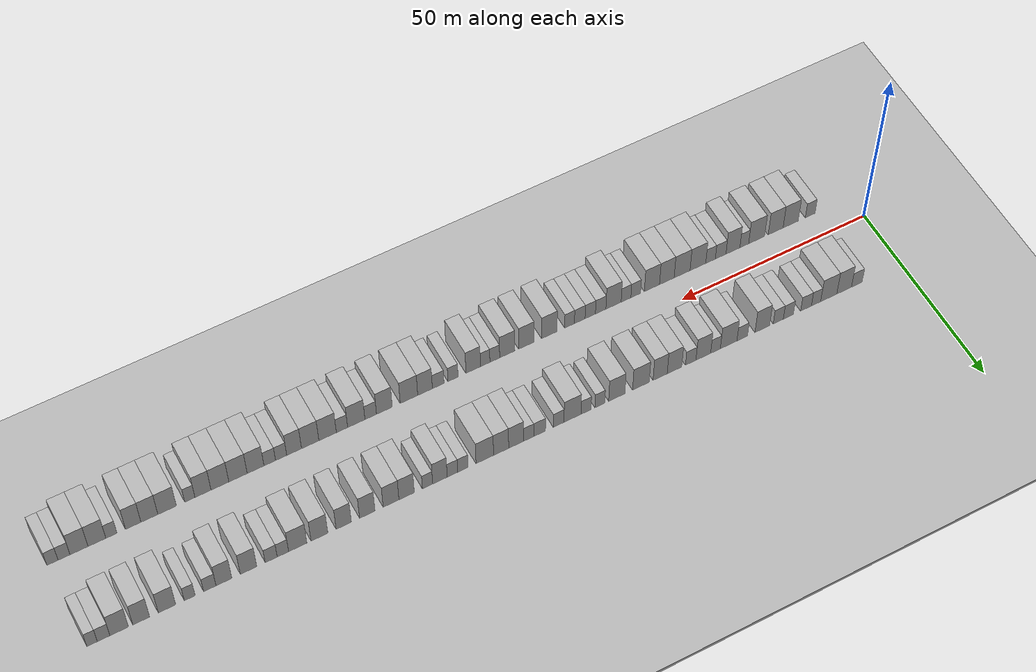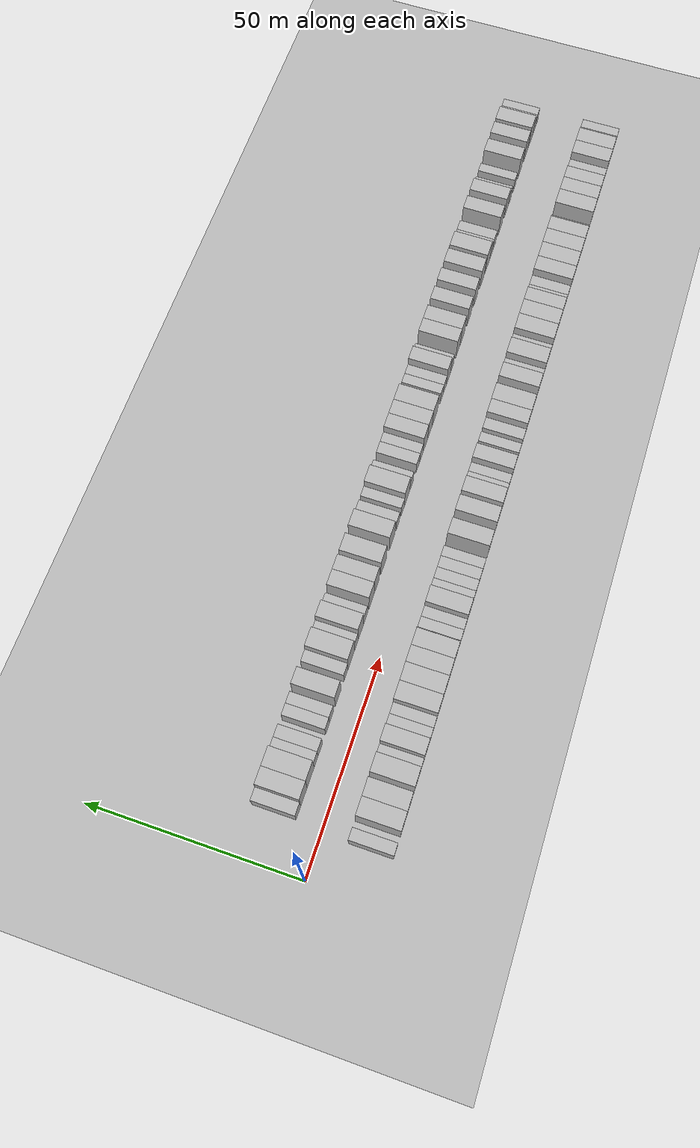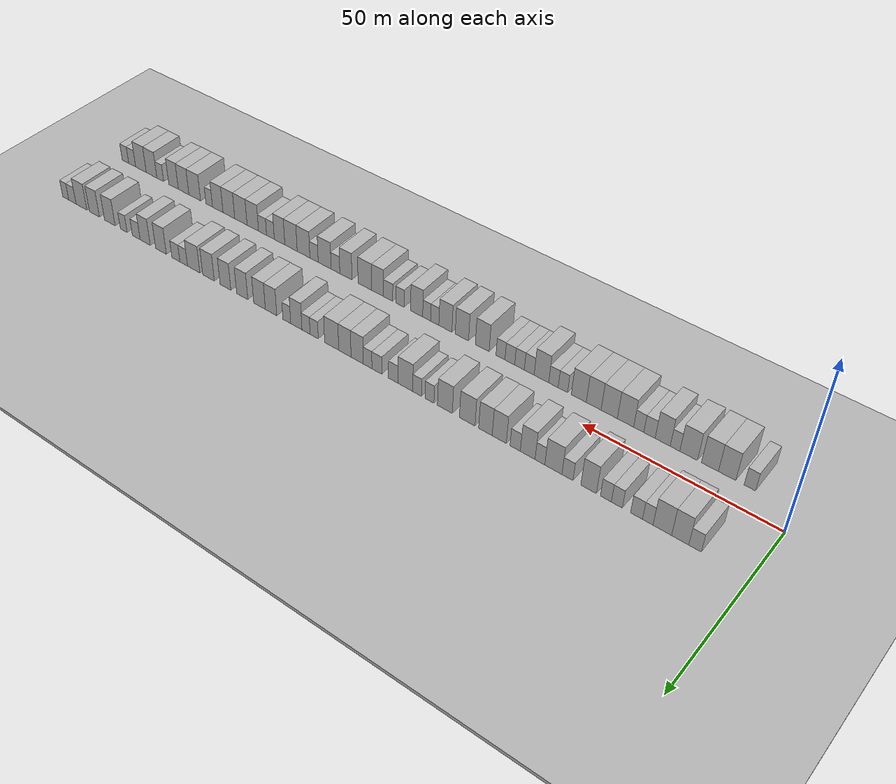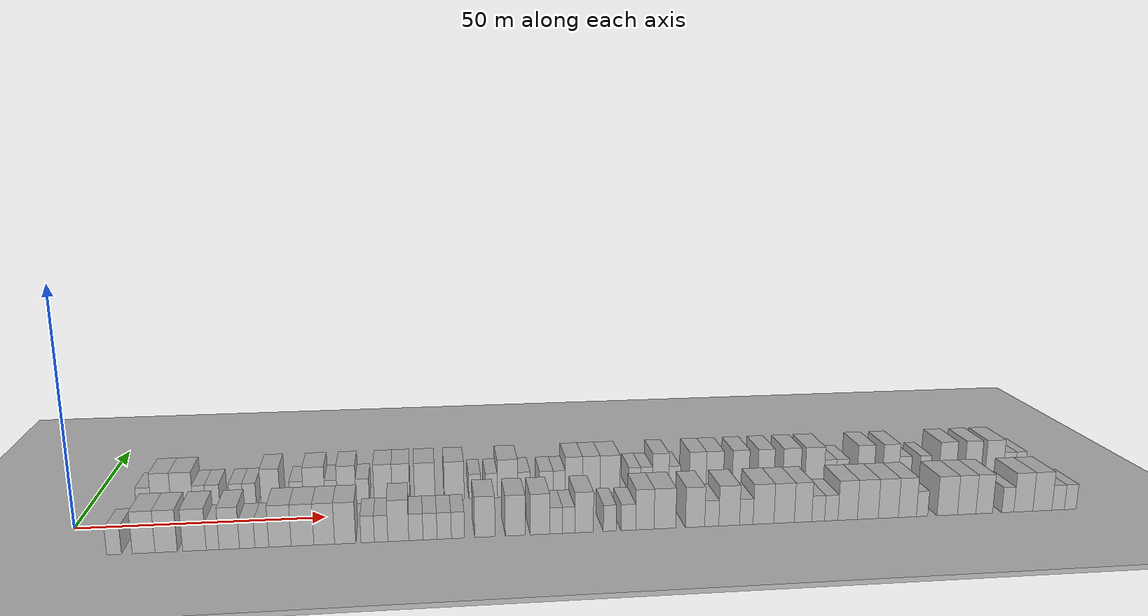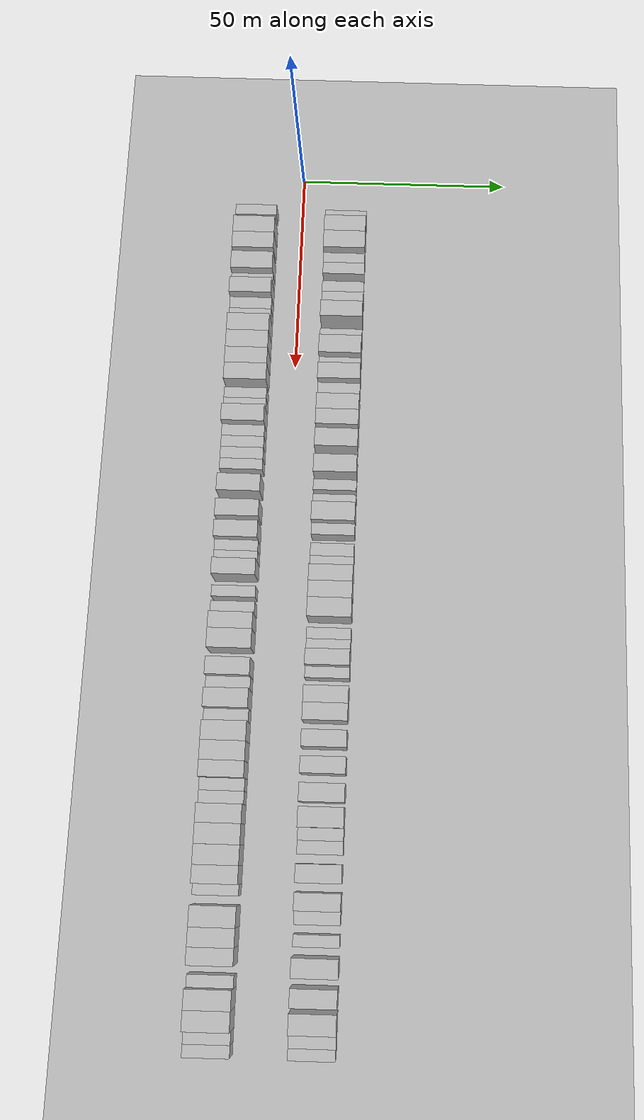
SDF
<?xml version="1.0" encoding="utf-8"?>

<sdf version="1.6">

   <world name="default">

      <gui fullscreen="0">

         <camera name="user_camera">

            <pose>-15 0 4.57585 0 0 0</pose>

            <view_controller>orbit</view_controller>

         </camera>

      </gui>

      <scene>

         <sky>

           <clouds>

             <speed>12</speed>

           </clouds>

         </sky>

         <ambient>0.4 0.4 0.4 1</ambient>

         <background>0.7 0.7 0.7 1</background>

         <shadows>1</shadows>

      </scene>

      <gravity>0 0 -9.8066</gravity>

      <magnetic_field>6e-06 2.3e-05 -4.2e-05</magnetic_field>

      <physics default="0" name="default_physics" type="ode">

         <ode>

            <solver>

               <type>quick</type>

               <iters>10</iters>

               <sor>1.0</sor>

               <use_dynamic_moi_rescaling>0</use_dynamic_moi_rescaling>

            </solver>

            <constraints>

               <cfm>0</cfm>

               <erp>0.2</erp>

               <contact_max_correcting_vel>100</contact_max_correcting_vel>

               <contact_surface_layer>0.001</contact_surface_layer>

            </constraints>

         </ode>

         <max_step_size>0.004</max_step_size>

         <real_time_factor>1</real_time_factor>

         <real_time_update_rate>250</real_time_update_rate>

      </physics>

      <light name="sun" type="directional">

         <cast_shadows>1</cast_shadows>

         <pose>0 0 10 0 0 0</pose>

         <diffuse>0.8 0.8 0.8 1</diffuse>

         <specular>0.2 0.2 0.2 1</specular>

         <attenuation>

            <range>1000</range>

            <constant>0.9</constant>

            <linear>0.01</linear>

            <quadratic>0.001</quadratic>

         </attenuation>

         <direction>-0.5 0.1 -0.9</direction>

      </light>

      <include>

         <name>ground_plane_1</name>

         <uri>model://HANNAS_ground_plane</uri>

         <pose>0 0 0  0 0 0</pose>

      </include>

      <include>

         <name>ground_plane_2</name>

         <uri>model://HANNAS_ground_plane</uri>

         <pose>100 0 0  0 0 0</pose>

      </include>

      <model name="building_1">

         <static>1</static>

         <pose frame="">12.4693 11.0000 0 0.000000 0.000000 1.570796</pose>

         <link name="link">

            <pose frame="">0 0 3.00 0 0 0</pose>

            <collision name="collision">

               <geometry>

                  <box>

                     <size>10.0000 2.9386 6.0000</size>

                  </box>

               </geometry>

               <max_contacts>10</max_contacts>

               <surface>

                  <contact>

                     <ode/>

                  </contact>

                  <bounce/>

                  <friction>

                     <torsional>

                        <ode/>

                     </torsional>

                     <ode/>

                  </friction>

               </surface>

            </collision>

            <visual name="visual">

               <cast_shadows>0</cast_shadows>

               <geometry>

                  <box>

                     <size>10.0000 2.9386 6.0000</size>

                  </box>

               </geometry>

               <material>

                  <script>

                     <uri>model://HANNAS_wall/materials/scripts</uri>

                     <uri>model://HANNAS_wall/materials/textures</uri>

                     <name>vrc/HANNAS_wall</name>

                  </script>

               </material>

            </visual>

            <self_collide>0</self_collide>

            <enable_wind>0</enable_wind>

            <kinematic>0</kinematic>

         </link>

      </model>

      <model name="building_2">

         <static>1</static>

         <pose frame="">15.9527 11.0000 0 0.000000 0.000000 1.570796</pose>

         <link name="link">

            <pose frame="">0 0 4.50 0 0 0</pose>

            <collision name="collision">

               <geometry>

                  <box>

                     <size>10.0000 4.0283 9.0000</size>

                  </box>

               </geometry>

               <max_contacts>10</max_contacts>

               <surface>

                  <contact>

                     <ode/>

                  </contact>

                  <bounce/>

                  <friction>

                     <torsional>

                        <ode/>

                     </torsional>

                     <ode/>

                  </friction>

               </surface>

            </collision>

            <visual name="visual">

               <cast_shadows>0</cast_shadows>

               <geometry>

                  <box>

                     <size>10.0000 4.0283 9.0000</size>

                  </box>

               </geometry>

               <material>

                  <script>

                     <uri>model://HANNAS_wall/materials/scripts</uri>

                     <uri>model://HANNAS_wall/materials/textures</uri>

                     <name>vrc/HANNAS_wall</name>

                  </script>

               </material>

            </visual>

            <self_collide>0</self_collide>

            <enable_wind>0</enable_wind>

            <kinematic>0</kinematic>

         </link>

      </model>

      <model name="building_3">

         <static>1</static>

         <pose frame="">20.1891 11.0000 0 0.000000 0.000000 1.570796</pose>

         <link name="link">

            <pose frame="">0 0 4.50 0 0 0</pose>

            <collision name="collision">

               <geometry>

                  <box>

                     <size>10.0000 4.4444 9.0000</size>

                  </box>

               </geometry>

               <max_contacts>10</max_contacts>

               <surface>

                  <contact>

                     <ode/>

                  </contact>

                  <bounce/>

                  <friction>

                     <torsional>

                        <ode/>

                     </torsional>

                     <ode/>

                  </friction>

               </surface>

            </collision>

            <visual name="visual">

               <cast_shadows>0</cast_shadows>

               <geometry>

                  <box>

                     <size>10.0000 4.4444 9.0000</size>

                  </box>

               </geometry>

               <material>

                  <script>

                     <uri>model://HANNAS_wall/materials/scripts</uri>

                     <uri>model://HANNAS_wall/materials/textures</uri>

                     <name>vrc/HANNAS_wall</name>

                  </script>

               </material>

            </visual>

            <self_collide>0</self_collide>

            <enable_wind>0</enable_wind>

            <kinematic>0</kinematic>

         </link>

      </model>

      <model name="building_4">

         <static>1</static>

         <pose frame="">23.6728 11.0000 0 0.000000 0.000000 1.570796</pose>

         <link name="link">

            <pose frame="">0 0 3.00 0 0 0</pose>

            <collision name="collision">

               <geometry>

                  <box>

                     <size>10.0000 2.5231 6.0000</size>

                  </box>

               </geometry>

               <max_contacts>10</max_contacts>

               <surface>

                  <contact>

                     <ode/>

                  </contact>

                  <bounce/>

                  <friction>

                     <torsional>

                        <ode/>

                     </torsional>

                     <ode/>

                  </friction>

               </surface>

            </collision>

            <visual name="visual">

               <cast_shadows>0</cast_shadows>

               <geometry>

                  <box>

                     <size>10.0000 2.5231 6.0000</size>

                  </box>

               </geometry>

               <material>

                  <script>

                     <uri>model://HANNAS_wall/materials/scripts</uri>

                     <uri>model://HANNAS_wall/materials/textures</uri>

                     <name>vrc/HANNAS_wall</name>

                  </script>

               </material>

            </visual>

            <self_collide>0</self_collide>

            <enable_wind>0</enable_wind>

            <kinematic>0</kinematic>

         </link>

      </model>

      <model name="building_5">

         <static>1</static>

         <pose frame="">26.3972 11.0000 0 0.000000 0.000000 1.570796</pose>

         <link name="link">

            <pose frame="">0 0 3.00 0 0 0</pose>

            <collision name="collision">

               <geometry>

                  <box>

                     <size>10.0000 2.9257 6.0000</size>

                  </box>

               </geometry>

               <max_contacts>10</max_contacts>

               <surface>

                  <contact>

                     <ode/>

                  </contact>

                  <bounce/>

                  <friction>

                     <torsional>

                        <ode/>

                     </torsional>

                     <ode/>

                  </friction>

               </surface>

            </collision>

            <visual name="visual">

               <cast_shadows>0</cast_shadows>

               <geometry>

                  <box>

                     <size>10.0000 2.9257 6.0000</size>

                  </box>

               </geometry>

               <material>

                  <script>

                     <uri>model://HANNAS_wall/materials/scripts</uri>

                     <uri>model://HANNAS_wall/materials/textures</uri>

                     <name>vrc/HANNAS_wall</name>

                  </script>

               </material>

            </visual>

            <self_collide>0</self_collide>

            <enable_wind>0</enable_wind>

            <kinematic>0</kinematic>

         </link>

      </model>

      <model name="building_6">

         <static>1</static>

         <pose frame="">31.2161 11.0000 0 0.000000 0.000000 1.570796</pose>

         <link name="link">

            <pose frame="">0 0 3.00 0 0 0</pose>

            <collision name="collision">

               <geometry>

                  <box>

                     <size>10.0000 2.7120 6.0000</size>

                  </box>

               </geometry>

               <max_contacts>10</max_contacts>

               <surface>

                  <contact>

                     <ode/>

                  </contact>

                  <bounce/>

                  <friction>

                     <torsional>

                        <ode/>

                     </torsional>

                     <ode/>

                  </friction>

               </surface>

            </collision>

            <visual name="visual">

               <cast_shadows>0</cast_shadows>

               <geometry>

                  <box>

                     <size>10.0000 2.7120 6.0000</size>

                  </box>

               </geometry>

               <material>

                  <script>

                     <uri>model://HANNAS_wall/materials/scripts</uri>

                     <uri>model://HANNAS_wall/materials/textures</uri>

                     <name>vrc/HANNAS_wall</name>

                  </script>

               </material>

            </visual>

            <self_collide>0</self_collide>

            <enable_wind>0</enable_wind>

            <kinematic>0</kinematic>

         </link>

      </model>

      <model name="building_7">

         <static>1</static>

         <pose frame="">33.9364 11.0000 0 0.000000 0.000000 1.570796</pose>

         <link name="link">

            <pose frame="">0 0 3.00 0 0 0</pose>

            <collision name="collision">

               <geometry>

                  <box>

                     <size>10.0000 2.7288 6.0000</size>

                  </box>

               </geometry>

               <max_contacts>10</max_contacts>

               <surface>

                  <contact>

                     <ode/>

                  </contact>

                  <bounce/>

                  <friction>

                     <torsional>

                        <ode/>

                     </torsional>

                     <ode/>

                  </friction>

               </surface>

            </collision>

            <visual name="visual">

               <cast_shadows>0</cast_shadows>

               <geometry>

                  <box>

                     <size>10.0000 2.7288 6.0000</size>

                  </box>

               </geometry>

               <material>

                  <script>

                     <uri>model://HANNAS_wall/materials/scripts</uri>

                     <uri>model://HANNAS_wall/materials/textures</uri>

                     <name>vrc/HANNAS_wall</name>

                  </script>

               </material>

            </visual>

            <self_collide>0</self_collide>

            <enable_wind>0</enable_wind>

            <kinematic>0</kinematic>

         </link>

      </model>

      <model name="building_8">

         <static>1</static>

         <pose frame="">38.2680 11.0000 0 0.000000 0.000000 1.570796</pose>

         <link name="link">

            <pose frame="">0 0 4.50 0 0 0</pose>

            <collision name="collision">

               <geometry>

                  <box>

                     <size>10.0000 3.9342 9.0000</size>

                  </box>

               </geometry>

               <max_contacts>10</max_contacts>

               <surface>

                  <contact>

                     <ode/>

                  </contact>

                  <bounce/>

                  <friction>

                     <torsional>

                        <ode/>

                     </torsional>

                     <ode/>

                  </friction>

               </surface>

            </collision>

            <visual name="visual">

               <cast_shadows>0</cast_shadows>

               <geometry>

                  <box>

                     <size>10.0000 3.9342 9.0000</size>

                  </box>

               </geometry>

               <material>

                  <script>

                     <uri>model://HANNAS_wall/materials/scripts</uri>

                     <uri>model://HANNAS_wall/materials/textures</uri>

                     <name>vrc/HANNAS_wall</name>

                  </script>

               </material>

            </visual>

            <self_collide>0</self_collide>

            <enable_wind>0</enable_wind>

            <kinematic>0</kinematic>

         </link>

      </model>

      <model name="building_9">

         <static>1</static>

         <pose frame="">43.6566 11.0000 0 0.000000 0.000000 1.570796</pose>

         <link name="link">

            <pose frame="">0 0 3.00 0 0 0</pose>

            <collision name="collision">

               <geometry>

                  <box>

                     <size>10.0000 2.8430 6.0000</size>

                  </box>

               </geometry>

               <max_contacts>10</max_contacts>

               <surface>

                  <contact>

                     <ode/>

                  </contact>

                  <bounce/>

                  <friction>

                     <torsional>

                        <ode/>

                     </torsional>

                     <ode/>

                  </friction>

               </surface>

            </collision>

            <visual name="visual">

               <cast_shadows>0</cast_shadows>

               <geometry>

                  <box>

                     <size>10.0000 2.8430 6.0000</size>

                  </box>

               </geometry>

               <material>

                  <script>

                     <uri>model://HANNAS_wall/materials/scripts</uri>

                     <uri>model://HANNAS_wall/materials/textures</uri>

                     <name>vrc/HANNAS_wall</name>

                  </script>

               </material>

            </visual>

            <self_collide>0</self_collide>

            <enable_wind>0</enable_wind>

            <kinematic>0</kinematic>

         </link>

      </model>

      <model name="building_10">

         <static>1</static>

         <pose frame="">47.2999 11.0000 0 0.000000 0.000000 1.570796</pose>

         <link name="link">

            <pose frame="">0 0 4.50 0 0 0</pose>

            <collision name="collision">

               <geometry>

                  <box>

                     <size>10.0000 4.4437 9.0000</size>

                  </box>

               </geometry>

               <max_contacts>10</max_contacts>

               <surface>

                  <contact>

                     <ode/>

                  </contact>

                  <bounce/>

                  <friction>

                     <torsional>

                        <ode/>

                     </torsional>

                     <ode/>

                  </friction>

               </surface>

            </collision>

            <visual name="visual">

               <cast_shadows>0</cast_shadows>

               <geometry>

                  <box>

                     <size>10.0000 4.4437 9.0000</size>

                  </box>

               </geometry>

               <material>

                  <script>

                     <uri>model://HANNAS_wall/materials/scripts</uri>

                     <uri>model://HANNAS_wall/materials/textures</uri>

                     <name>vrc/HANNAS_wall</name>

                  </script>

               </material>

            </visual>

            <self_collide>0</self_collide>

            <enable_wind>0</enable_wind>

            <kinematic>0</kinematic>

         </link>

      </model>

      <model name="building_11">

         <static>1</static>

         <pose frame="">50.7997 11.0000 0 0.000000 0.000000 1.570796</pose>

         <link name="link">

            <pose frame="">0 0 3.00 0 0 0</pose>

            <collision name="collision">

               <geometry>

                  <box>

                     <size>10.0000 2.5560 6.0000</size>

                  </box>

               </geometry>

               <max_contacts>10</max_contacts>

               <surface>

                  <contact>

                     <ode/>

                  </contact>

                  <bounce/>

                  <friction>

                     <torsional>

                        <ode/>

                     </torsional>

                     <ode/>

                  </friction>

               </surface>

            </collision>

            <visual name="visual">

               <cast_shadows>0</cast_shadows>

               <geometry>

                  <box>

                     <size>10.0000 2.5560 6.0000</size>

                  </box>

               </geometry>

               <material>

                  <script>

                     <uri>model://HANNAS_wall/materials/scripts</uri>

                     <uri>model://HANNAS_wall/materials/textures</uri>

                     <name>vrc/HANNAS_wall</name>

                  </script>

               </material>

            </visual>

            <self_collide>0</self_collide>

            <enable_wind>0</enable_wind>

            <kinematic>0</kinematic>

         </link>

      </model>

      <model name="building_12">

         <static>1</static>

         <pose frame="">54.0382 11.0000 0 0.000000 0.000000 1.570796</pose>

         <link name="link">

            <pose frame="">0 0 4.50 0 0 0</pose>

            <collision name="collision">

               <geometry>

                  <box>

                     <size>10.0000 3.9210 9.0000</size>

                  </box>

               </geometry>

               <max_contacts>10</max_contacts>

               <surface>

                  <contact>

                     <ode/>

                  </contact>

                  <bounce/>

                  <friction>

                     <torsional>

                        <ode/>

                     </torsional>

                     <ode/>

                  </friction>

               </surface>

            </collision>

            <visual name="visual">

               <cast_shadows>0</cast_shadows>

               <geometry>

                  <box>

                     <size>10.0000 3.9210 9.0000</size>

                  </box>

               </geometry>

               <material>

                  <script>

                     <uri>model://HANNAS_wall/materials/scripts</uri>

                     <uri>model://HANNAS_wall/materials/textures</uri>

                     <name>vrc/HANNAS_wall</name>

                  </script>

               </material>

            </visual>

            <self_collide>0</self_collide>

            <enable_wind>0</enable_wind>

            <kinematic>0</kinematic>

         </link>

      </model>

      <model name="building_13">

         <static>1</static>

         <pose frame="">57.3779 11.0000 0 0.000000 0.000000 1.570796</pose>

         <link name="link">

            <pose frame="">0 0 3.00 0 0 0</pose>

            <collision name="collision">

               <geometry>

                  <box>

                     <size>10.0000 2.7582 6.0000</size>

                  </box>

               </geometry>

               <max_contacts>10</max_contacts>

               <surface>

                  <contact>

                     <ode/>

                  </contact>

                  <bounce/>

                  <friction>

                     <torsional>

                        <ode/>

                     </torsional>

                     <ode/>

                  </friction>

               </surface>

            </collision>

            <visual name="visual">

               <cast_shadows>0</cast_shadows>

               <geometry>

                  <box>

                     <size>10.0000 2.7582 6.0000</size>

                  </box>

               </geometry>

               <material>

                  <script>

                     <uri>model://HANNAS_wall/materials/scripts</uri>

                     <uri>model://HANNAS_wall/materials/textures</uri>

                     <name>vrc/HANNAS_wall</name>

                  </script>

               </material>

            </visual>

            <self_collide>0</self_collide>

            <enable_wind>0</enable_wind>

            <kinematic>0</kinematic>

         </link>

      </model>

      <model name="building_14">

         <static>1</static>

         <pose frame="">61.6745 11.0000 0 0.000000 0.000000 1.570796</pose>

         <link name="link">

            <pose frame="">0 0 4.50 0 0 0</pose>

            <collision name="collision">

               <geometry>

                  <box>

                     <size>10.0000 3.8351 9.0000</size>

                  </box>

               </geometry>

               <max_contacts>10</max_contacts>

               <surface>

                  <contact>

                     <ode/>

                  </contact>

                  <bounce/>

                  <friction>

                     <torsional>

                        <ode/>

                     </torsional>

                     <ode/>

                  </friction>

               </surface>

            </collision>

            <visual name="visual">

               <cast_shadows>0</cast_shadows>

               <geometry>

                  <box>

                     <size>10.0000 3.8351 9.0000</size>

                  </box>

               </geometry>

               <material>

                  <script>

                     <uri>model://HANNAS_wall/materials/scripts</uri>

                     <uri>model://HANNAS_wall/materials/textures</uri>

                     <name>vrc/HANNAS_wall</name>

                  </script>

               </material>

            </visual>

            <self_collide>0</self_collide>

            <enable_wind>0</enable_wind>

            <kinematic>0</kinematic>

         </link>

      </model>

      <model name="building_15">

         <static>1</static>

         <pose frame="">65.4515 11.0000 0 0.000000 0.000000 1.570796</pose>

         <link name="link">

            <pose frame="">0 0 4.50 0 0 0</pose>

            <collision name="collision">

               <geometry>

                  <box>

                     <size>10.0000 3.7188 9.0000</size>

                  </box>

               </geometry>

               <max_contacts>10</max_contacts>

               <surface>

                  <contact>

                     <ode/>

                  </contact>

                  <bounce/>

                  <friction>

                     <torsional>

                        <ode/>

                     </torsional>

                     <ode/>

                  </friction>

               </surface>

            </collision>

            <visual name="visual">

               <cast_shadows>0</cast_shadows>

               <geometry>

                  <box>

                     <size>10.0000 3.7188 9.0000</size>

                  </box>

               </geometry>

               <material>

                  <script>

                     <uri>model://HANNAS_wall/materials/scripts</uri>

                     <uri>model://HANNAS_wall/materials/textures</uri>

                     <name>vrc/HANNAS_wall</name>

                  </script>

               </material>

            </visual>

            <self_collide>0</self_collide>

            <enable_wind>0</enable_wind>

            <kinematic>0</kinematic>

         </link>

      </model>

      <model name="building_16">

         <static>1</static>

         <pose frame="">70.4830 11.0000 0 0.000000 0.000000 1.570796</pose>

         <link name="link">

            <pose frame="">0 0 4.50 0 0 0</pose>

            <collision name="collision">

               <geometry>

                  <box>

                     <size>10.0000 4.3443 9.0000</size>

                  </box>

               </geometry>

               <max_contacts>10</max_contacts>

               <surface>

                  <contact>

                     <ode/>

                  </contact>

                  <bounce/>

                  <friction>

                     <torsional>

                        <ode/>

                     </torsional>

                     <ode/>

                  </friction>

               </surface>

            </collision>

            <visual name="visual">

               <cast_shadows>0</cast_shadows>

               <geometry>

                  <box>

                     <size>10.0000 4.3443 9.0000</size>

                  </box>

               </geometry>

               <material>

                  <script>

                     <uri>model://HANNAS_wall/materials/scripts</uri>

                     <uri>model://HANNAS_wall/materials/textures</uri>

                     <name>vrc/HANNAS_wall</name>

                  </script>

               </material>

            </visual>

            <self_collide>0</self_collide>

            <enable_wind>0</enable_wind>

            <kinematic>0</kinematic>

         </link>

      </model>

      <model name="building_17">

         <static>1</static>

         <pose frame="">76.7704 11.0000 0 0.000000 0.000000 1.570796</pose>

         <link name="link">

            <pose frame="">0 0 4.50 0 0 0</pose>

            <collision name="collision">

               <geometry>

                  <box>

                     <size>10.0000 4.2305 9.0000</size>

                  </box>

               </geometry>

               <max_contacts>10</max_contacts>

               <surface>

                  <contact>

                     <ode/>

                  </contact>

                  <bounce/>

                  <friction>

                     <torsional>

                        <ode/>

                     </torsional>

                     <ode/>

                  </friction>

               </surface>

            </collision>

            <visual name="visual">

               <cast_shadows>0</cast_shadows>

               <geometry>

                  <box>

                     <size>10.0000 4.2305 9.0000</size>

                  </box>

               </geometry>

               <material>

                  <script>

                     <uri>model://HANNAS_wall/materials/scripts</uri>

                     <uri>model://HANNAS_wall/materials/textures</uri>

                     <name>vrc/HANNAS_wall</name>

                  </script>

               </material>

            </visual>

            <self_collide>0</self_collide>

            <enable_wind>0</enable_wind>

            <kinematic>0</kinematic>

         </link>

      </model>

      <model name="building_18">

         <static>1</static>

         <pose frame="">81.1689 11.0000 0 0.000000 0.000000 1.570796</pose>

         <link name="link">

            <pose frame="">0 0 3.00 0 0 0</pose>

            <collision name="collision">

               <geometry>

                  <box>

                     <size>10.0000 2.5665 6.0000</size>

                  </box>

               </geometry>

               <max_contacts>10</max_contacts>

               <surface>

                  <contact>

                     <ode/>

                  </contact>

                  <bounce/>

                  <friction>

                     <torsional>

                        <ode/>

                     </torsional>

                     <ode/>

                  </friction>

               </surface>

            </collision>

            <visual name="visual">

               <cast_shadows>0</cast_shadows>

               <geometry>

                  <box>

                     <size>10.0000 2.5665 6.0000</size>

                  </box>

               </geometry>

               <material>

                  <script>

                     <uri>model://HANNAS_wall/materials/scripts</uri>

                     <uri>model://HANNAS_wall/materials/textures</uri>

                     <name>vrc/HANNAS_wall</name>

                  </script>

               </material>

            </visual>

            <self_collide>0</self_collide>

            <enable_wind>0</enable_wind>

            <kinematic>0</kinematic>

         </link>

      </model>

      <model name="building_19">

         <static>1</static>

         <pose frame="">84.7434 11.0000 0 0.000000 0.000000 1.570796</pose>

         <link name="link">

            <pose frame="">0 0 3.00 0 0 0</pose>

            <collision name="collision">

               <geometry>

                  <box>

                     <size>10.0000 2.5826 6.0000</size>

                  </box>

               </geometry>

               <max_contacts>10</max_contacts>

               <surface>

                  <contact>

                     <ode/>

                  </contact>

                  <bounce/>

                  <friction>

                     <torsional>

                        <ode/>

                     </torsional>

                     <ode/>

                  </friction>

               </surface>

            </collision>

            <visual name="visual">

               <cast_shadows>0</cast_shadows>

               <geometry>

                  <box>

                     <size>10.0000 2.5826 6.0000</size>

                  </box>

               </geometry>

               <material>

                  <script>

                     <uri>model://HANNAS_wall/materials/scripts</uri>

                     <uri>model://HANNAS_wall/materials/textures</uri>

                     <name>vrc/HANNAS_wall</name>

                  </script>

               </material>

            </visual>

            <self_collide>0</self_collide>

            <enable_wind>0</enable_wind>

            <kinematic>0</kinematic>

         </link>

      </model>

      <model name="building_20">

         <static>1</static>

         <pose frame="">88.2218 11.0000 0 0.000000 0.000000 1.570796</pose>

         <link name="link">

            <pose frame="">0 0 4.50 0 0 0</pose>

            <collision name="collision">

               <geometry>

                  <box>

                     <size>10.0000 4.3742 9.0000</size>

                  </box>

               </geometry>

               <max_contacts>10</max_contacts>

               <surface>

                  <contact>

                     <ode/>

                  </contact>

                  <bounce/>

                  <friction>

                     <torsional>

                        <ode/>

                     </torsional>

                     <ode/>

                  </friction>

               </surface>

            </collision>

            <visual name="visual">

               <cast_shadows>0</cast_shadows>

               <geometry>

                  <box>

                     <size>10.0000 4.3742 9.0000</size>

                  </box>

               </geometry>

               <material>

                  <script>

                     <uri>model://HANNAS_wall/materials/scripts</uri>

                     <uri>model://HANNAS_wall/materials/textures</uri>

                     <name>vrc/HANNAS_wall</name>

                  </script>

               </material>

            </visual>

            <self_collide>0</self_collide>

            <enable_wind>0</enable_wind>

            <kinematic>0</kinematic>

         </link>

      </model>

      <model name="building_21">

         <static>1</static>

         <pose frame="">91.7784 11.0000 0 0.000000 0.000000 1.570796</pose>

         <link name="link">

            <pose frame="">0 0 3.00 0 0 0</pose>

            <collision name="collision">

               <geometry>

                  <box>

                     <size>10.0000 2.7390 6.0000</size>

                  </box>

               </geometry>

               <max_contacts>10</max_contacts>

               <surface>

                  <contact>

                     <ode/>

                  </contact>

                  <bounce/>

                  <friction>

                     <torsional>

                        <ode/>

                     </torsional>

                     <ode/>

                  </friction>

               </surface>

            </collision>

            <visual name="visual">

               <cast_shadows>0</cast_shadows>

               <geometry>

                  <box>

                     <size>10.0000 2.7390 6.0000</size>

                  </box>

               </geometry>

               <material>

                  <script>

                     <uri>model://HANNAS_wall/materials/scripts</uri>

                     <uri>model://HANNAS_wall/materials/textures</uri>

                     <name>vrc/HANNAS_wall</name>

                  </script>

               </material>

            </visual>

            <self_collide>0</self_collide>

            <enable_wind>0</enable_wind>

            <kinematic>0</kinematic>

         </link>

      </model>

      <model name="building_22">

         <static>1</static>

         <pose frame="">96.6448 11.0000 0 0.000000 0.000000 1.570796</pose>

         <link name="link">

            <pose frame="">0 0 3.00 0 0 0</pose>

            <collision name="collision">

               <geometry>

                  <box>

                     <size>10.0000 2.9938 6.0000</size>

                  </box>

               </geometry>

               <max_contacts>10</max_contacts>

               <surface>

                  <contact>

                     <ode/>

                  </contact>

                  <bounce/>

                  <friction>

                     <torsional>

                        <ode/>

                     </torsional>

                     <ode/>

                  </friction>

               </surface>

            </collision>

            <visual name="visual">

               <cast_shadows>0</cast_shadows>

               <geometry>

                  <box>

                     <size>10.0000 2.9938 6.0000</size>

                  </box>

               </geometry>

               <material>

                  <script>

                     <uri>model://HANNAS_wall/materials/scripts</uri>

                     <uri>model://HANNAS_wall/materials/textures</uri>

                     <name>vrc/HANNAS_wall</name>

                  </script>

               </material>

            </visual>

            <self_collide>0</self_collide>

            <enable_wind>0</enable_wind>

            <kinematic>0</kinematic>

         </link>

      </model>

      <model name="building_23">

         <static>1</static>

         <pose frame="">99.4413 11.0000 0 0.000000 0.000000 1.570796</pose>

         <link name="link">

            <pose frame="">0 0 3.00 0 0 0</pose>

            <collision name="collision">

               <geometry>

                  <box>

                     <size>10.0000 2.5992 6.0000</size>

                  </box>

               </geometry>

               <max_contacts>10</max_contacts>

               <surface>

                  <contact>

                     <ode/>

                  </contact>

                  <bounce/>

                  <friction>

                     <torsional>

                        <ode/>

                     </torsional>

                     <ode/>

                  </friction>

               </surface>

            </collision>

            <visual name="visual">

               <cast_shadows>0</cast_shadows>

               <geometry>

                  <box>

                     <size>10.0000 2.5992 6.0000</size>

                  </box>

               </geometry>

               <material>

                  <script>

                     <uri>model://HANNAS_wall/materials/scripts</uri>

                     <uri>model://HANNAS_wall/materials/textures</uri>

                     <name>vrc/HANNAS_wall</name>

                  </script>

               </material>

            </visual>

            <self_collide>0</self_collide>

            <enable_wind>0</enable_wind>

            <kinematic>0</kinematic>

         </link>

      </model>

      <model name="building_24">

         <static>1</static>

         <pose frame="">102.6171 11.0000 0 0.000000 0.000000 1.570796</pose>

         <link name="link">

            <pose frame="">0 0 4.50 0 0 0</pose>

            <collision name="collision">

               <geometry>

                  <box>

                     <size>10.0000 3.7523 9.0000</size>

                  </box>

               </geometry>

               <max_contacts>10</max_contacts>

               <surface>

                  <contact>

                     <ode/>

                  </contact>

                  <bounce/>

                  <friction>

                     <torsional>

                        <ode/>

                     </torsional>

                     <ode/>

                  </friction>

               </surface>

            </collision>

            <visual name="visual">

               <cast_shadows>0</cast_shadows>

               <geometry>

                  <box>

                     <size>10.0000 3.7523 9.0000</size>

                  </box>

               </geometry>

               <material>

                  <script>

                     <uri>model://HANNAS_wall/materials/scripts</uri>

                     <uri>model://HANNAS_wall/materials/textures</uri>

                     <name>vrc/HANNAS_wall</name>

                  </script>

               </material>

            </visual>

            <self_collide>0</self_collide>

            <enable_wind>0</enable_wind>

            <kinematic>0</kinematic>

         </link>

      </model>

      <model name="building_25">

         <static>1</static>

         <pose frame="">106.4064 11.0000 0 0.000000 0.000000 1.570796</pose>

         <link name="link">

            <pose frame="">0 0 4.50 0 0 0</pose>

            <collision name="collision">

               <geometry>

                  <box>

                     <size>10.0000 3.8263 9.0000</size>

                  </box>

               </geometry>

               <max_contacts>10</max_contacts>

               <surface>

                  <contact>

                     <ode/>

                  </contact>

                  <bounce/>

                  <friction>

                     <torsional>

                        <ode/>

                     </torsional>

                     <ode/>

                  </friction>

               </surface>

            </collision>

            <visual name="visual">

               <cast_shadows>0</cast_shadows>

               <geometry>

                  <box>

                     <size>10.0000 3.8263 9.0000</size>

                  </box>

               </geometry>

               <material>

                  <script>

                     <uri>model://HANNAS_wall/materials/scripts</uri>

                     <uri>model://HANNAS_wall/materials/textures</uri>

                     <name>vrc/HANNAS_wall</name>

                  </script>

               </material>

            </visual>

            <self_collide>0</self_collide>

            <enable_wind>0</enable_wind>

            <kinematic>0</kinematic>

         </link>

      </model>

      <model name="building_26">

         <static>1</static>

         <pose frame="">110.5225 11.0000 0 0.000000 0.000000 1.570796</pose>

         <link name="link">

            <pose frame="">0 0 4.50 0 0 0</pose>

            <collision name="collision">

               <geometry>

                  <box>

                     <size>10.0000 4.4060 9.0000</size>

                  </box>

               </geometry>

               <max_contacts>10</max_contacts>

               <surface>

                  <contact>

                     <ode/>

                  </contact>

                  <bounce/>

                  <friction>

                     <torsional>

                        <ode/>

                     </torsional>

                     <ode/>

                  </friction>

               </surface>

            </collision>

            <visual name="visual">

               <cast_shadows>0</cast_shadows>

               <geometry>

                  <box>

                     <size>10.0000 4.4060 9.0000</size>

                  </box>

               </geometry>

               <material>

                  <script>

                     <uri>model://HANNAS_wall/materials/scripts</uri>

                     <uri>model://HANNAS_wall/materials/textures</uri>

                     <name>vrc/HANNAS_wall</name>

                  </script>

               </material>

            </visual>

            <self_collide>0</self_collide>

            <enable_wind>0</enable_wind>

            <kinematic>0</kinematic>

         </link>

      </model>

      <model name="building_27">

         <static>1</static>

         <pose frame="">116.0191 11.0000 0 0.000000 0.000000 1.570796</pose>

         <link name="link">

            <pose frame="">0 0 3.00 0 0 0</pose>

            <collision name="collision">

               <geometry>

                  <box>

                     <size>10.0000 2.5871 6.0000</size>

                  </box>

               </geometry>

               <max_contacts>10</max_contacts>

               <surface>

                  <contact>

                     <ode/>

                  </contact>

                  <bounce/>

                  <friction>

                     <torsional>

                        <ode/>

                     </torsional>

                     <ode/>

                  </friction>

               </surface>

            </collision>

            <visual name="visual">

               <cast_shadows>0</cast_shadows>

               <geometry>

                  <box>

                     <size>10.0000 2.5871 6.0000</size>

                  </box>

               </geometry>

               <material>

                  <script>

                     <uri>model://HANNAS_wall/materials/scripts</uri>

                     <uri>model://HANNAS_wall/materials/textures</uri>

                     <name>vrc/HANNAS_wall</name>

                  </script>

               </material>

            </visual>

            <self_collide>0</self_collide>

            <enable_wind>0</enable_wind>

            <kinematic>0</kinematic>

         </link>

      </model>

      <model name="building_28">

         <static>1</static>

         <pose frame="">118.6194 11.0000 0 0.000000 0.000000 1.570796</pose>

         <link name="link">

            <pose frame="">0 0 3.00 0 0 0</pose>

            <collision name="collision">

               <geometry>

                  <box>

                     <size>10.0000 2.6136 6.0000</size>

                  </box>

               </geometry>

               <max_contacts>10</max_contacts>

               <surface>

                  <contact>

                     <ode/>

                  </contact>

                  <bounce/>

                  <friction>

                     <torsional>

                        <ode/>

                     </torsional>

                     <ode/>

                  </friction>

               </surface>

            </collision>

            <visual name="visual">

               <cast_shadows>0</cast_shadows>

               <geometry>

                  <box>

                     <size>10.0000 2.6136 6.0000</size>

                  </box>

               </geometry>

               <material>

                  <script>

                     <uri>model://HANNAS_wall/materials/scripts</uri>

                     <uri>model://HANNAS_wall/materials/textures</uri>

                     <name>vrc/HANNAS_wall</name>

                  </script>

               </material>

            </visual>

            <self_collide>0</self_collide>

            <enable_wind>0</enable_wind>

            <kinematic>0</kinematic>

         </link>

      </model>

      <model name="building_29">

         <static>1</static>

         <pose frame="">121.7357 11.0000 0 0.000000 0.000000 1.570796</pose>

         <link name="link">

            <pose frame="">0 0 4.50 0 0 0</pose>

            <collision name="collision">

               <geometry>

                  <box>

                     <size>10.0000 3.6191 9.0000</size>

                  </box>

               </geometry>

               <max_contacts>10</max_contacts>

               <surface>

                  <contact>

                     <ode/>

                  </contact>

                  <bounce/>

                  <friction>

                     <torsional>

                        <ode/>

                     </torsional>

                     <ode/>

                  </friction>

               </surface>

            </collision>

            <visual name="visual">

               <cast_shadows>0</cast_shadows>

               <geometry>

                  <box>

                     <size>10.0000 3.6191 9.0000</size>

                  </box>

               </geometry>

               <material>

                  <script>

                     <uri>model://HANNAS_wall/materials/scripts</uri>

                     <uri>model://HANNAS_wall/materials/textures</uri>

                     <name>vrc/HANNAS_wall</name>

                  </script>

               </material>

            </visual>

            <self_collide>0</self_collide>

            <enable_wind>0</enable_wind>

            <kinematic>0</kinematic>

         </link>

      </model>

      <model name="building_30">

         <static>1</static>

         <pose frame="">124.8204 11.0000 0 0.000000 0.000000 1.570796</pose>

         <link name="link">

            <pose frame="">0 0 3.00 0 0 0</pose>

            <collision name="collision">

               <geometry>

                  <box>

                     <size>10.0000 2.5502 6.0000</size>

                  </box>

               </geometry>

               <max_contacts>10</max_contacts>

               <surface>

                  <contact>

                     <ode/>

                  </contact>

                  <bounce/>

                  <friction>

                     <torsional>

                        <ode/>

                     </torsional>

                     <ode/>

                  </friction>

               </surface>

            </collision>

            <visual name="visual">

               <cast_shadows>0</cast_shadows>

               <geometry>

                  <box>

                     <size>10.0000 2.5502 6.0000</size>

                  </box>

               </geometry>

               <material>

                  <script>

                     <uri>model://HANNAS_wall/materials/scripts</uri>

                     <uri>model://HANNAS_wall/materials/textures</uri>

                     <name>vrc/HANNAS_wall</name>

                  </script>

               </material>

            </visual>

            <self_collide>0</self_collide>

            <enable_wind>0</enable_wind>

            <kinematic>0</kinematic>

         </link>

      </model>

      <model name="building_31">

         <static>1</static>

         <pose frame="">129.9866 11.0000 0 0.000000 0.000000 1.570796</pose>

         <link name="link">

            <pose frame="">0 0 4.50 0 0 0</pose>

            <collision name="collision">

               <geometry>

                  <box>

                     <size>10.0000 3.7824 9.0000</size>

                  </box>

               </geometry>

               <max_contacts>10</max_contacts>

               <surface>

                  <contact>

                     <ode/>

                  </contact>

                  <bounce/>

                  <friction>

                     <torsional>

                        <ode/>

                     </torsional>

                     <ode/>

                  </friction>

               </surface>

            </collision>

            <visual name="visual">

               <cast_shadows>0</cast_shadows>

               <geometry>

                  <box>

                     <size>10.0000 3.7824 9.0000</size>

                  </box>

               </geometry>

               <material>

                  <script>

                     <uri>model://HANNAS_wall/materials/scripts</uri>

                     <uri>model://HANNAS_wall/materials/textures</uri>

                     <name>vrc/HANNAS_wall</name>

                  </script>

               </material>

            </visual>

            <self_collide>0</self_collide>

            <enable_wind>0</enable_wind>

            <kinematic>0</kinematic>

         </link>

      </model>

      <model name="building_32">

         <static>1</static>

         <pose frame="">133.8148 11.0000 0 0.000000 0.000000 1.570796</pose>

         <link name="link">

            <pose frame="">0 0 4.50 0 0 0</pose>

            <collision name="collision">

               <geometry>

                  <box>

                     <size>10.0000 3.8740 9.0000</size>

                  </box>

               </geometry>

               <max_contacts>10</max_contacts>

               <surface>

                  <contact>

                     <ode/>

                  </contact>

                  <bounce/>

                  <friction>

                     <torsional>

                        <ode/>

                     </torsional>

                     <ode/>

                  </friction>

               </surface>

            </collision>

            <visual name="visual">

               <cast_shadows>0</cast_shadows>

               <geometry>

                  <box>

                     <size>10.0000 3.8740 9.0000</size>

                  </box>

               </geometry>

               <material>

                  <script>

                     <uri>model://HANNAS_wall/materials/scripts</uri>

                     <uri>model://HANNAS_wall/materials/textures</uri>

                     <name>vrc/HANNAS_wall</name>

                  </script>

               </material>

            </visual>

            <self_collide>0</self_collide>

            <enable_wind>0</enable_wind>

            <kinematic>0</kinematic>

         </link>

      </model>

      <model name="building_33">

         <static>1</static>

         <pose frame="">139.6373 11.0000 0 0.000000 0.000000 1.570796</pose>

         <link name="link">

            <pose frame="">0 0 4.50 0 0 0</pose>

            <collision name="collision">

               <geometry>

                  <box>

                     <size>10.0000 3.7710 9.0000</size>

                  </box>

               </geometry>

               <max_contacts>10</max_contacts>

               <surface>

                  <contact>

                     <ode/>

                  </contact>

                  <bounce/>

                  <friction>

                     <torsional>

                        <ode/>

                     </torsional>

                     <ode/>

                  </friction>

               </surface>

            </collision>

            <visual name="visual">

               <cast_shadows>0</cast_shadows>

               <geometry>

                  <box>

                     <size>10.0000 3.7710 9.0000</size>

                  </box>

               </geometry>

               <material>

                  <script>

                     <uri>model://HANNAS_wall/materials/scripts</uri>

                     <uri>model://HANNAS_wall/materials/textures</uri>

                     <name>vrc/HANNAS_wall</name>

                  </script>

               </material>

            </visual>

            <self_collide>0</self_collide>

            <enable_wind>0</enable_wind>

            <kinematic>0</kinematic>

         </link>

      </model>

      <model name="building_34">

         <static>1</static>

         <pose frame="">145.3760 11.0000 0 0.000000 0.000000 1.570796</pose>

         <link name="link">

            <pose frame="">0 0 4.50 0 0 0</pose>

            <collision name="collision">

               <geometry>

                  <box>

                     <size>10.0000 3.7065 9.0000</size>

                  </box>

               </geometry>

               <max_contacts>10</max_contacts>

               <surface>

                  <contact>

                     <ode/>

                  </contact>

                  <bounce/>

                  <friction>

                     <torsional>

                        <ode/>

                     </torsional>

                     <ode/>

                  </friction>

               </surface>

            </collision>

            <visual name="visual">

               <cast_shadows>0</cast_shadows>

               <geometry>

                  <box>

                     <size>10.0000 3.7065 9.0000</size>

                  </box>

               </geometry>

               <material>

                  <script>

                     <uri>model://HANNAS_wall/materials/scripts</uri>

                     <uri>model://HANNAS_wall/materials/textures</uri>

                     <name>vrc/HANNAS_wall</name>

                  </script>

               </material>

            </visual>

            <self_collide>0</self_collide>

            <enable_wind>0</enable_wind>

            <kinematic>0</kinematic>

         </link>

      </model>

      <model name="building_35">

         <static>1</static>

         <pose frame="">151.2617 11.0000 0 0.000000 0.000000 1.570796</pose>

         <link name="link">

            <pose frame="">0 0 4.50 0 0 0</pose>

            <collision name="collision">

               <geometry>

                  <box>

                     <size>10.0000 4.0648 9.0000</size>

                  </box>

               </geometry>

               <max_contacts>10</max_contacts>

               <surface>

                  <contact>

                     <ode/>

                  </contact>

                  <bounce/>

                  <friction>

                     <torsional>

                        <ode/>

                     </torsional>

                     <ode/>

                  </friction>

               </surface>

            </collision>

            <visual name="visual">

               <cast_shadows>0</cast_shadows>

               <geometry>

                  <box>

                     <size>10.0000 4.0648 9.0000</size>

                  </box>

               </geometry>

               <material>

                  <script>

                     <uri>model://HANNAS_wall/materials/scripts</uri>

                     <uri>model://HANNAS_wall/materials/textures</uri>

                     <name>vrc/HANNAS_wall</name>

                  </script>

               </material>

            </visual>

            <self_collide>0</self_collide>

            <enable_wind>0</enable_wind>

            <kinematic>0</kinematic>

         </link>

      </model>

      <model name="building_36">

         <static>1</static>

         <pose frame="">156.4872 11.0000 0 0.000000 0.000000 1.570796</pose>

         <link name="link">

            <pose frame="">0 0 4.50 0 0 0</pose>

            <collision name="collision">

               <geometry>

                  <box>

                     <size>10.0000 4.3862 9.0000</size>

                  </box>

               </geometry>

               <max_contacts>10</max_contacts>

               <surface>

                  <contact>

                     <ode/>

                  </contact>

                  <bounce/>

                  <friction>

                     <torsional>

                        <ode/>

                     </torsional>

                     <ode/>

                  </friction>

               </surface>

            </collision>

            <visual name="visual">

               <cast_shadows>0</cast_shadows>

               <geometry>

                  <box>

                     <size>10.0000 4.3862 9.0000</size>

                  </box>

               </geometry>

               <material>

                  <script>

                     <uri>model://HANNAS_wall/materials/scripts</uri>

                     <uri>model://HANNAS_wall/materials/textures</uri>

                     <name>vrc/HANNAS_wall</name>

                  </script>

               </material>

            </visual>

            <self_collide>0</self_collide>

            <enable_wind>0</enable_wind>

            <kinematic>0</kinematic>

         </link>

      </model>

      <model name="building_37">

         <static>1</static>

         <pose frame="">160.0484 11.0000 0 0.000000 0.000000 1.570796</pose>

         <link name="link">

            <pose frame="">0 0 3.00 0 0 0</pose>

            <collision name="collision">

               <geometry>

                  <box>

                     <size>10.0000 2.7362 6.0000</size>

                  </box>

               </geometry>

               <max_contacts>10</max_contacts>

               <surface>

                  <contact>

                     <ode/>

                  </contact>

                  <bounce/>

                  <friction>

                     <torsional>

                        <ode/>

                     </torsional>

                     <ode/>

                  </friction>

               </surface>

            </collision>

            <visual name="visual">

               <cast_shadows>0</cast_shadows>

               <geometry>

                  <box>

                     <size>10.0000 2.7362 6.0000</size>

                  </box>

               </geometry>

               <material>

                  <script>

                     <uri>model://HANNAS_wall/materials/scripts</uri>

                     <uri>model://HANNAS_wall/materials/textures</uri>

                     <name>vrc/HANNAS_wall</name>

                  </script>

               </material>

            </visual>

            <self_collide>0</self_collide>

            <enable_wind>0</enable_wind>

            <kinematic>0</kinematic>

         </link>

      </model>

      <model name="building_38">

         <static>1</static>

         <pose frame="">162.8559 11.0000 0 0.000000 0.000000 1.570796</pose>

         <link name="link">

            <pose frame="">0 0 3.00 0 0 0</pose>

            <collision name="collision">

               <geometry>

                  <box>

                     <size>10.0000 2.8789 6.0000</size>

                  </box>

               </geometry>

               <max_contacts>10</max_contacts>

               <surface>

                  <contact>

                     <ode/>

                  </contact>

                  <bounce/>

                  <friction>

                     <torsional>

                        <ode/>

                     </torsional>

                     <ode/>

                  </friction>

               </surface>

            </collision>

            <visual name="visual">

               <cast_shadows>0</cast_shadows>

               <geometry>

                  <box>

                     <size>10.0000 2.8789 6.0000</size>

                  </box>

               </geometry>

               <material>

                  <script>

                     <uri>model://HANNAS_wall/materials/scripts</uri>

                     <uri>model://HANNAS_wall/materials/textures</uri>

                     <name>vrc/HANNAS_wall</name>

                  </script>

               </material>

            </visual>

            <self_collide>0</self_collide>

            <enable_wind>0</enable_wind>

            <kinematic>0</kinematic>

         </link>

      </model>

      <model name="building_39">

         <static>1</static>

         <pose frame="">168.2533 11.0000 0 0.000000 0.000000 1.570796</pose>

         <link name="link">

            <pose frame="">0 0 4.50 0 0 0</pose>

            <collision name="collision">

               <geometry>

                  <box>

                     <size>10.0000 3.9160 9.0000</size>

                  </box>

               </geometry>

               <max_contacts>10</max_contacts>

               <surface>

                  <contact>

                     <ode/>

                  </contact>

                  <bounce/>

                  <friction>

                     <torsional>

                        <ode/>

                     </torsional>

                     <ode/>

                  </friction>

               </surface>

            </collision>

            <visual name="visual">

               <cast_shadows>0</cast_shadows>

               <geometry>

                  <box>

                     <size>10.0000 3.9160 9.0000</size>

                  </box>

               </geometry>

               <material>

                  <script>

                     <uri>model://HANNAS_wall/materials/scripts</uri>

                     <uri>model://HANNAS_wall/materials/textures</uri>

                     <name>vrc/HANNAS_wall</name>

                  </script>

               </material>

            </visual>

            <self_collide>0</self_collide>

            <enable_wind>0</enable_wind>

            <kinematic>0</kinematic>

         </link>

      </model>

      <model name="building_40">

         <static>1</static>

         <pose frame="">174.0844 11.0000 0 0.000000 0.000000 1.570796</pose>

         <link name="link">

            <pose frame="">0 0 4.50 0 0 0</pose>

            <collision name="collision">

               <geometry>

                  <box>

                     <size>10.0000 3.7462 9.0000</size>

                  </box>

               </geometry>

               <max_contacts>10</max_contacts>

               <surface>

                  <contact>

                     <ode/>

                  </contact>

                  <bounce/>

                  <friction>

                     <torsional>

                        <ode/>

                     </torsional>

                     <ode/>

                  </friction>

               </surface>

            </collision>

            <visual name="visual">

               <cast_shadows>0</cast_shadows>

               <geometry>

                  <box>

                     <size>10.0000 3.7462 9.0000</size>

                  </box>

               </geometry>

               <material>

                  <script>

                     <uri>model://HANNAS_wall/materials/scripts</uri>

                     <uri>model://HANNAS_wall/materials/textures</uri>

                     <name>vrc/HANNAS_wall</name>

                  </script>

               </material>

            </visual>

            <self_collide>0</self_collide>

            <enable_wind>0</enable_wind>

            <kinematic>0</kinematic>

         </link>

      </model>

      <model name="building_41">

         <static>1</static>

         <pose frame="">177.4131 11.0000 0 0.000000 0.000000 1.570796</pose>

         <link name="link">

            <pose frame="">0 0 3.00 0 0 0</pose>

            <collision name="collision">

               <geometry>

                  <box>

                     <size>10.0000 2.9111 6.0000</size>

                  </box>

               </geometry>

               <max_contacts>10</max_contacts>

               <surface>

                  <contact>

                     <ode/>

                  </contact>

                  <bounce/>

                  <friction>

                     <torsional>

                        <ode/>

                     </torsional>

                     <ode/>

                  </friction>

               </surface>

            </collision>

            <visual name="visual">

               <cast_shadows>0</cast_shadows>

               <geometry>

                  <box>

                     <size>10.0000 2.9111 6.0000</size>

                  </box>

               </geometry>

               <material>

                  <script>

                     <uri>model://HANNAS_wall/materials/scripts</uri>

                     <uri>model://HANNAS_wall/materials/textures</uri>

                     <name>vrc/HANNAS_wall</name>

                  </script>

               </material>

            </visual>

            <self_collide>0</self_collide>

            <enable_wind>0</enable_wind>

            <kinematic>0</kinematic>

         </link>

      </model>

      <model name="building_42">

         <static>1</static>

         <pose frame="">182.1428 11.0000 0 0.000000 0.000000 1.570796</pose>

         <link name="link">

            <pose frame="">0 0 3.00 0 0 0</pose>

            <collision name="collision">

               <geometry>

                  <box>

                     <size>10.0000 2.5483 6.0000</size>

                  </box>

               </geometry>

               <max_contacts>10</max_contacts>

               <surface>

                  <contact>

                     <ode/>

                  </contact>

                  <bounce/>

                  <friction>

                     <torsional>

                        <ode/>

                     </torsional>

                     <ode/>

                  </friction>

               </surface>

            </collision>

            <visual name="visual">

               <cast_shadows>0</cast_shadows>

               <geometry>

                  <box>

                     <size>10.0000 2.5483 6.0000</size>

                  </box>

               </geometry>

               <material>

                  <script>

                     <uri>model://HANNAS_wall/materials/scripts</uri>

                     <uri>model://HANNAS_wall/materials/textures</uri>

                     <name>vrc/HANNAS_wall</name>

                  </script>

               </material>

            </visual>

            <self_collide>0</self_collide>

            <enable_wind>0</enable_wind>

            <kinematic>0</kinematic>

         </link>

      </model>

      <model name="building_43">

         <static>1</static>

         <pose frame="">187.4469 11.0000 0 0.000000 0.000000 1.570796</pose>

         <link name="link">

            <pose frame="">0 0 4.50 0 0 0</pose>

            <collision name="collision">

               <geometry>

                  <box>

                     <size>10.0000 4.0600 9.0000</size>

                  </box>

               </geometry>

               <max_contacts>10</max_contacts>

               <surface>

                  <contact>

                     <ode/>

                  </contact>

                  <bounce/>

                  <friction>

                     <torsional>

                        <ode/>

                     </torsional>

                     <ode/>

                  </friction>

               </surface>

            </collision>

            <visual name="visual">

               <cast_shadows>0</cast_shadows>

               <geometry>

                  <box>

                     <size>10.0000 4.0600 9.0000</size>

                  </box>

               </geometry>

               <material>

                  <script>

                     <uri>model://HANNAS_wall/materials/scripts</uri>

                     <uri>model://HANNAS_wall/materials/textures</uri>

                     <name>vrc/HANNAS_wall</name>

                  </script>

               </material>

            </visual>

            <self_collide>0</self_collide>

            <enable_wind>0</enable_wind>

            <kinematic>0</kinematic>

         </link>

      </model>

      <model name="building_44">

         <static>1</static>

         <pose frame="">193.4263 11.0000 0 0.000000 0.000000 1.570796</pose>

         <link name="link">

            <pose frame="">0 0 4.50 0 0 0</pose>

            <collision name="collision">

               <geometry>

                  <box>

                     <size>10.0000 3.8988 9.0000</size>

                  </box>

               </geometry>

               <max_contacts>10</max_contacts>

               <surface>

                  <contact>

                     <ode/>

                  </contact>

                  <bounce/>

                  <friction>

                     <torsional>

                        <ode/>

                     </torsional>

                     <ode/>

                  </friction>

               </surface>

            </collision>

            <visual name="visual">

               <cast_shadows>0</cast_shadows>

               <geometry>

                  <box>

                     <size>10.0000 3.8988 9.0000</size>

                  </box>

               </geometry>

               <material>

                  <script>

                     <uri>model://HANNAS_wall/materials/scripts</uri>

                     <uri>model://HANNAS_wall/materials/textures</uri>

                     <name>vrc/HANNAS_wall</name>

                  </script>

               </material>

            </visual>

            <self_collide>0</self_collide>

            <enable_wind>0</enable_wind>

            <kinematic>0</kinematic>

         </link>

      </model>

      <model name="building_45">

         <static>1</static>

         <pose frame="">198.5137 11.0000 0 0.000000 0.000000 1.570796</pose>

         <link name="link">

            <pose frame="">0 0 4.50 0 0 0</pose>

            <collision name="collision">

               <geometry>

                  <box>

                     <size>10.0000 4.2759 9.0000</size>

                  </box>

               </geometry>

               <max_contacts>10</max_contacts>

               <surface>

                  <contact>

                     <ode/>

                  </contact>

                  <bounce/>

                  <friction>

                     <torsional>

                        <ode/>

                     </torsional>

                     <ode/>

                  </friction>

               </surface>

            </collision>

            <visual name="visual">

               <cast_shadows>0</cast_shadows>

               <geometry>

                  <box>

                     <size>10.0000 4.2759 9.0000</size>

                  </box>

               </geometry>

               <material>

                  <script>

                     <uri>model://HANNAS_wall/materials/scripts</uri>

                     <uri>model://HANNAS_wall/materials/textures</uri>

                     <name>vrc/HANNAS_wall</name>

                  </script>

               </material>

            </visual>

            <self_collide>0</self_collide>

            <enable_wind>0</enable_wind>

            <kinematic>0</kinematic>

         </link>

      </model>

      <model name="building_46">

         <static>1</static>

         <pose frame="">202.1068 11.0000 0 0.000000 0.000000 1.570796</pose>

         <link name="link">

            <pose frame="">0 0 3.00 0 0 0</pose>

            <collision name="collision">

               <geometry>

                  <box>

                     <size>10.0000 2.9104 6.0000</size>

                  </box>

               </geometry>

               <max_contacts>10</max_contacts>

               <surface>

                  <contact>

                     <ode/>

                  </contact>

                  <bounce/>

                  <friction>

                     <torsional>

                        <ode/>

                     </torsional>

                     <ode/>

                  </friction>

               </surface>

            </collision>

            <visual name="visual">

               <cast_shadows>0</cast_shadows>

               <geometry>

                  <box>

                     <size>10.0000 2.9104 6.0000</size>

                  </box>

               </geometry>

               <material>

                  <script>

                     <uri>model://HANNAS_wall/materials/scripts</uri>

                     <uri>model://HANNAS_wall/materials/textures</uri>

                     <name>vrc/HANNAS_wall</name>

                  </script>

               </material>

            </visual>

            <self_collide>0</self_collide>

            <enable_wind>0</enable_wind>

            <kinematic>0</kinematic>

         </link>

      </model>

      <model name="building_47">

         <static>1</static>

         <pose frame="">204.7638 11.0000 0 0.000000 0.000000 1.570796</pose>

         <link name="link">

            <pose frame="">0 0 3.00 0 0 0</pose>

            <collision name="collision">

               <geometry>

                  <box>

                     <size>10.0000 2.4036 6.0000</size>

                  </box>

               </geometry>

               <max_contacts>10</max_contacts>

               <surface>

                  <contact>

                     <ode/>

                  </contact>

                  <bounce/>

                  <friction>

                     <torsional>

                        <ode/>

                     </torsional>

                     <ode/>

                  </friction>

               </surface>

            </collision>

            <visual name="visual">

               <cast_shadows>0</cast_shadows>

               <geometry>

                  <box>

                     <size>10.0000 2.4036 6.0000</size>

                  </box>

               </geometry>

               <material>

                  <script>

                     <uri>model://HANNAS_wall/materials/scripts</uri>

                     <uri>model://HANNAS_wall/materials/textures</uri>

                     <name>vrc/HANNAS_wall</name>

                  </script>

               </material>

            </visual>

            <self_collide>0</self_collide>

            <enable_wind>0</enable_wind>

            <kinematic>0</kinematic>

         </link>

      </model>

      <model name="building_48">

         <static>1</static>

         <pose frame="">11.3614 -11.0000 0 0.000000 0.000000 1.570796</pose>

         <link name="link">

            <pose frame="">0 0 3.00 0 0 0</pose>

            <collision name="collision">

               <geometry>

                  <box>

                     <size>10.0000 2.7227 6.0000</size>

                  </box>

               </geometry>

               <max_contacts>10</max_contacts>

               <surface>

                  <contact>

                     <ode/>

                  </contact>

                  <bounce/>

                  <friction>

                     <torsional>

                        <ode/>

                     </torsional>

                     <ode/>

                  </friction>

               </surface>

            </collision>

            <visual name="visual">

               <cast_shadows>0</cast_shadows>

               <geometry>

                  <box>

                     <size>10.0000 2.7227 6.0000</size>

                  </box>

               </geometry>

               <material>

                  <script>

                     <uri>model://HANNAS_wall/materials/scripts</uri>

                     <uri>model://HANNAS_wall/materials/textures</uri>

                     <name>vrc/HANNAS_wall</name>

                  </script>

               </material>

            </visual>

            <self_collide>0</self_collide>

            <enable_wind>0</enable_wind>

            <kinematic>0</kinematic>

         </link>

      </model>

      <model name="building_49">

         <static>1</static>

         <pose frame="">16.8233 -11.0000 0 0.000000 0.000000 1.570796</pose>

         <link name="link">

            <pose frame="">0 0 4.50 0 0 0</pose>

            <collision name="collision">

               <geometry>

                  <box>

                     <size>10.0000 4.2013 9.0000</size>

                  </box>

               </geometry>

               <max_contacts>10</max_contacts>

               <surface>

                  <contact>

                     <ode/>

                  </contact>

                  <bounce/>

                  <friction>

                     <torsional>

                        <ode/>

                     </torsional>

                     <ode/>

                  </friction>

               </surface>

            </collision>

            <visual name="visual">

               <cast_shadows>0</cast_shadows>

               <geometry>

                  <box>

                     <size>10.0000 4.2013 9.0000</size>

                  </box>

               </geometry>

               <material>

                  <script>

                     <uri>model://HANNAS_wall/materials/scripts</uri>

                     <uri>model://HANNAS_wall/materials/textures</uri>

                     <name>vrc/HANNAS_wall</name>

                  </script>

               </material>

            </visual>

            <self_collide>0</self_collide>

            <enable_wind>0</enable_wind>

            <kinematic>0</kinematic>

         </link>

      </model>

      <model name="building_50">

         <static>1</static>

         <pose frame="">20.9922 -11.0000 0 0.000000 0.000000 1.570796</pose>

         <link name="link">

            <pose frame="">0 0 4.50 0 0 0</pose>

            <collision name="collision">

               <geometry>

                  <box>

                     <size>10.0000 4.1364 9.0000</size>

                  </box>

               </geometry>

               <max_contacts>10</max_contacts>

               <surface>

                  <contact>

                     <ode/>

                  </contact>

                  <bounce/>

                  <friction>

                     <torsional>

                        <ode/>

                     </torsional>

                     <ode/>

                  </friction>

               </surface>

            </collision>

            <visual name="visual">

               <cast_shadows>0</cast_shadows>

               <geometry>

                  <box>

                     <size>10.0000 4.1364 9.0000</size>

                  </box>

               </geometry>

               <material>

                  <script>

                     <uri>model://HANNAS_wall/materials/scripts</uri>

                     <uri>model://HANNAS_wall/materials/textures</uri>

                     <name>vrc/HANNAS_wall</name>

                  </script>

               </material>

            </visual>

            <self_collide>0</self_collide>

            <enable_wind>0</enable_wind>

            <kinematic>0</kinematic>

         </link>

      </model>

      <model name="building_51">

         <static>1</static>

         <pose frame="">26.2591 -11.0000 0 0.000000 0.000000 1.570796</pose>

         <link name="link">

            <pose frame="">0 0 4.50 0 0 0</pose>

            <collision name="collision">

               <geometry>

                  <box>

                     <size>10.0000 4.3973 9.0000</size>

                  </box>

               </geometry>

               <max_contacts>10</max_contacts>

               <surface>

                  <contact>

                     <ode/>

                  </contact>

                  <bounce/>

                  <friction>

                     <torsional>

                        <ode/>

                     </torsional>

                     <ode/>

                  </friction>

               </surface>

            </collision>

            <visual name="visual">

               <cast_shadows>0</cast_shadows>

               <geometry>

                  <box>

                     <size>10.0000 4.3973 9.0000</size>

                  </box>

               </geometry>

               <material>

                  <script>

                     <uri>model://HANNAS_wall/materials/scripts</uri>

                     <uri>model://HANNAS_wall/materials/textures</uri>

                     <name>vrc/HANNAS_wall</name>

                  </script>

               </material>

            </visual>

            <self_collide>0</self_collide>

            <enable_wind>0</enable_wind>

            <kinematic>0</kinematic>

         </link>

      </model>

      <model name="building_52">

         <static>1</static>

         <pose frame="">29.6619 -11.0000 0 0.000000 0.000000 1.570796</pose>

         <link name="link">

            <pose frame="">0 0 3.00 0 0 0</pose>

            <collision name="collision">

               <geometry>

                  <box>

                     <size>10.0000 2.4083 6.0000</size>

                  </box>

               </geometry>

               <max_contacts>10</max_contacts>

               <surface>

                  <contact>

                     <ode/>

                  </contact>

                  <bounce/>

                  <friction>

                     <torsional>

                        <ode/>

                     </torsional>

                     <ode/>

                  </friction>

               </surface>

            </collision>

            <visual name="visual">

               <cast_shadows>0</cast_shadows>

               <geometry>

                  <box>

                     <size>10.0000 2.4083 6.0000</size>

                  </box>

               </geometry>

               <material>

                  <script>

                     <uri>model://HANNAS_wall/materials/scripts</uri>

                     <uri>model://HANNAS_wall/materials/textures</uri>

                     <name>vrc/HANNAS_wall</name>

                  </script>

               </material>

            </visual>

            <self_collide>0</self_collide>

            <enable_wind>0</enable_wind>

            <kinematic>0</kinematic>

         </link>

      </model>

      <model name="building_53">

         <static>1</static>

         <pose frame="">32.7780 -11.0000 0 0.000000 0.000000 1.570796</pose>

         <link name="link">

            <pose frame="">0 0 4.50 0 0 0</pose>

            <collision name="collision">

               <geometry>

                  <box>

                     <size>10.0000 3.8241 9.0000</size>

                  </box>

               </geometry>

               <max_contacts>10</max_contacts>

               <surface>

                  <contact>

                     <ode/>

                  </contact>

                  <bounce/>

                  <friction>

                     <torsional>

                        <ode/>

                     </torsional>

                     <ode/>

                  </friction>

               </surface>

            </collision>

            <visual name="visual">

               <cast_shadows>0</cast_shadows>

               <geometry>

                  <box>

                     <size>10.0000 3.8241 9.0000</size>

                  </box>

               </geometry>

               <material>

                  <script>

                     <uri>model://HANNAS_wall/materials/scripts</uri>

                     <uri>model://HANNAS_wall/materials/textures</uri>

                     <name>vrc/HANNAS_wall</name>

                  </script>

               </material>

            </visual>

            <self_collide>0</self_collide>

            <enable_wind>0</enable_wind>

            <kinematic>0</kinematic>

         </link>

      </model>

      <model name="building_54">

         <static>1</static>

         <pose frame="">36.1393 -11.0000 0 0.000000 0.000000 1.570796</pose>

         <link name="link">

            <pose frame="">0 0 3.00 0 0 0</pose>

            <collision name="collision">

               <geometry>

                  <box>

                     <size>10.0000 2.8985 6.0000</size>

                  </box>

               </geometry>

               <max_contacts>10</max_contacts>

               <surface>

                  <contact>

                     <ode/>

                  </contact>

                  <bounce/>

                  <friction>

                     <torsional>

                        <ode/>

                     </torsional>

                     <ode/>

                  </friction>

               </surface>

            </collision>

            <visual name="visual">

               <cast_shadows>0</cast_shadows>

               <geometry>

                  <box>

                     <size>10.0000 2.8985 6.0000</size>

                  </box>

               </geometry>

               <material>

                  <script>

                     <uri>model://HANNAS_wall/materials/scripts</uri>

                     <uri>model://HANNAS_wall/materials/textures</uri>

                     <name>vrc/HANNAS_wall</name>

                  </script>

               </material>

            </visual>

            <self_collide>0</self_collide>

            <enable_wind>0</enable_wind>

            <kinematic>0</kinematic>

         </link>

      </model>

      <model name="building_55">

         <static>1</static>

         <pose frame="">38.9028 -11.0000 0 0.000000 0.000000 1.570796</pose>

         <link name="link">

            <pose frame="">0 0 3.00 0 0 0</pose>

            <collision name="collision">

               <geometry>

                  <box>

                     <size>10.0000 2.6283 6.0000</size>

                  </box>

               </geometry>

               <max_contacts>10</max_contacts>

               <surface>

                  <contact>

                     <ode/>

                  </contact>

                  <bounce/>

                  <friction>

                     <torsional>

                        <ode/>

                     </torsional>

                     <ode/>

                  </friction>

               </surface>

            </collision>

            <visual name="visual">

               <cast_shadows>0</cast_shadows>

               <geometry>

                  <box>

                     <size>10.0000 2.6283 6.0000</size>

                  </box>

               </geometry>

               <material>

                  <script>

                     <uri>model://HANNAS_wall/materials/scripts</uri>

                     <uri>model://HANNAS_wall/materials/textures</uri>

                     <name>vrc/HANNAS_wall</name>

                  </script>

               </material>

            </visual>

            <self_collide>0</self_collide>

            <enable_wind>0</enable_wind>

            <kinematic>0</kinematic>

         </link>

      </model>

      <model name="building_56">

         <static>1</static>

         <pose frame="">42.3489 -11.0000 0 0.000000 0.000000 1.570796</pose>

         <link name="link">

            <pose frame="">0 0 4.50 0 0 0</pose>

            <collision name="collision">

               <geometry>

                  <box>

                     <size>10.0000 4.2639 9.0000</size>

                  </box>

               </geometry>

               <max_contacts>10</max_contacts>

               <surface>

                  <contact>

                     <ode/>

                  </contact>

                  <bounce/>

                  <friction>

                     <torsional>

                        <ode/>

                     </torsional>

                     <ode/>

                  </friction>

               </surface>

            </collision>

            <visual name="visual">

               <cast_shadows>0</cast_shadows>

               <geometry>

                  <box>

                     <size>10.0000 4.2639 9.0000</size>

                  </box>

               </geometry>

               <material>

                  <script>

                     <uri>model://HANNAS_wall/materials/scripts</uri>

                     <uri>model://HANNAS_wall/materials/textures</uri>

                     <name>vrc/HANNAS_wall</name>

                  </script>

               </material>

            </visual>

            <self_collide>0</self_collide>

            <enable_wind>0</enable_wind>

            <kinematic>0</kinematic>

         </link>

      </model>

      <model name="building_57">

         <static>1</static>

         <pose frame="">46.6372 -11.0000 0 0.000000 0.000000 1.570796</pose>

         <link name="link">

            <pose frame="">0 0 4.50 0 0 0</pose>

            <collision name="collision">

               <geometry>

                  <box>

                     <size>10.0000 4.3127 9.0000</size>

                  </box>

               </geometry>

               <max_contacts>10</max_contacts>

               <surface>

                  <contact>

                     <ode/>

                  </contact>

                  <bounce/>

                  <friction>

                     <torsional>

                        <ode/>

                     </torsional>

                     <ode/>

                  </friction>

               </surface>

            </collision>

            <visual name="visual">

               <cast_shadows>0</cast_shadows>

               <geometry>

                  <box>

                     <size>10.0000 4.3127 9.0000</size>

                  </box>

               </geometry>

               <material>

                  <script>

                     <uri>model://HANNAS_wall/materials/scripts</uri>

                     <uri>model://HANNAS_wall/materials/textures</uri>

                     <name>vrc/HANNAS_wall</name>

                  </script>

               </material>

            </visual>

            <self_collide>0</self_collide>

            <enable_wind>0</enable_wind>

            <kinematic>0</kinematic>

         </link>

      </model>

      <model name="building_58">

         <static>1</static>

         <pose frame="">50.7692 -11.0000 0 0.000000 0.000000 1.570796</pose>

         <link name="link">

            <pose frame="">0 0 4.50 0 0 0</pose>

            <collision name="collision">

               <geometry>

                  <box>

                     <size>10.0000 3.9514 9.0000</size>

                  </box>

               </geometry>

               <max_contacts>10</max_contacts>

               <surface>

                  <contact>

                     <ode/>

                  </contact>

                  <bounce/>

                  <friction>

                     <torsional>

                        <ode/>

                     </torsional>

                     <ode/>

                  </friction>

               </surface>

            </collision>

            <visual name="visual">

               <cast_shadows>0</cast_shadows>

               <geometry>

                  <box>

                     <size>10.0000 3.9514 9.0000</size>

                  </box>

               </geometry>

               <material>

                  <script>

                     <uri>model://HANNAS_wall/materials/scripts</uri>

                     <uri>model://HANNAS_wall/materials/textures</uri>

                     <name>vrc/HANNAS_wall</name>

                  </script>

               </material>

            </visual>

            <self_collide>0</self_collide>

            <enable_wind>0</enable_wind>

            <kinematic>0</kinematic>

         </link>

      </model>

      <model name="building_59">

         <static>1</static>

         <pose frame="">54.7804 -11.0000 0 0.000000 0.000000 1.570796</pose>

         <link name="link">

            <pose frame="">0 0 4.50 0 0 0</pose>

            <collision name="collision">

               <geometry>

                  <box>

                     <size>10.0000 4.0710 9.0000</size>

                  </box>

               </geometry>

               <max_contacts>10</max_contacts>

               <surface>

                  <contact>

                     <ode/>

                  </contact>

                  <bounce/>

                  <friction>

                     <torsional>

                        <ode/>

                     </torsional>

                     <ode/>

                  </friction>

               </surface>

            </collision>

            <visual name="visual">

               <cast_shadows>0</cast_shadows>

               <geometry>

                  <box>

                     <size>10.0000 4.0710 9.0000</size>

                  </box>

               </geometry>

               <material>

                  <script>

                     <uri>model://HANNAS_wall/materials/scripts</uri>

                     <uri>model://HANNAS_wall/materials/textures</uri>

                     <name>vrc/HANNAS_wall</name>

                  </script>

               </material>

            </visual>

            <self_collide>0</self_collide>

            <enable_wind>0</enable_wind>

            <kinematic>0</kinematic>

         </link>

      </model>

      <model name="building_60">

         <static>1</static>

         <pose frame="">59.1129 -11.0000 0 0.000000 0.000000 1.570796</pose>

         <link name="link">

            <pose frame="">0 0 3.00 0 0 0</pose>

            <collision name="collision">

               <geometry>

                  <box>

                     <size>10.0000 2.5940 6.0000</size>

                  </box>

               </geometry>

               <max_contacts>10</max_contacts>

               <surface>

                  <contact>

                     <ode/>

                  </contact>

                  <bounce/>

                  <friction>

                     <torsional>

                        <ode/>

                     </torsional>

                     <ode/>

                  </friction>

               </surface>

            </collision>

            <visual name="visual">

               <cast_shadows>0</cast_shadows>

               <geometry>

                  <box>

                     <size>10.0000 2.5940 6.0000</size>

                  </box>

               </geometry>

               <material>

                  <script>

                     <uri>model://HANNAS_wall/materials/scripts</uri>

                     <uri>model://HANNAS_wall/materials/textures</uri>

                     <name>vrc/HANNAS_wall</name>

                  </script>

               </material>

            </visual>

            <self_collide>0</self_collide>

            <enable_wind>0</enable_wind>

            <kinematic>0</kinematic>

         </link>

      </model>

      <model name="building_61">

         <static>1</static>

         <pose frame="">61.7125 -11.0000 0 0.000000 0.000000 1.570796</pose>

         <link name="link">

            <pose frame="">0 0 3.00 0 0 0</pose>

            <collision name="collision">

               <geometry>

                  <box>

                     <size>10.0000 2.6053 6.0000</size>

                  </box>

               </geometry>

               <max_contacts>10</max_contacts>

               <surface>

                  <contact>

                     <ode/>

                  </contact>

                  <bounce/>

                  <friction>

                     <torsional>

                        <ode/>

                     </torsional>

                     <ode/>

                  </friction>

               </surface>

            </collision>

            <visual name="visual">

               <cast_shadows>0</cast_shadows>

               <geometry>

                  <box>

                     <size>10.0000 2.6053 6.0000</size>

                  </box>

               </geometry>

               <material>

                  <script>

                     <uri>model://HANNAS_wall/materials/scripts</uri>

                     <uri>model://HANNAS_wall/materials/textures</uri>

                     <name>vrc/HANNAS_wall</name>

                  </script>

               </material>

            </visual>

            <self_collide>0</self_collide>

            <enable_wind>0</enable_wind>

            <kinematic>0</kinematic>

         </link>

      </model>

      <model name="building_62">

         <static>1</static>

         <pose frame="">65.0497 -11.0000 0 0.000000 0.000000 1.570796</pose>

         <link name="link">

            <pose frame="">0 0 4.50 0 0 0</pose>

            <collision name="collision">

               <geometry>

                  <box>

                     <size>10.0000 4.0690 9.0000</size>

                  </box>

               </geometry>

               <max_contacts>10</max_contacts>

               <surface>

                  <contact>

                     <ode/>

                  </contact>

                  <bounce/>

                  <friction>

                     <torsional>

                        <ode/>

                     </torsional>

                     <ode/>

                  </friction>

               </surface>

            </collision>

            <visual name="visual">

               <cast_shadows>0</cast_shadows>

               <geometry>

                  <box>

                     <size>10.0000 4.0690 9.0000</size>

                  </box>

               </geometry>

               <material>

                  <script>

                     <uri>model://HANNAS_wall/materials/scripts</uri>

                     <uri>model://HANNAS_wall/materials/textures</uri>

                     <name>vrc/HANNAS_wall</name>

                  </script>

               </material>

            </visual>

            <self_collide>0</self_collide>

            <enable_wind>0</enable_wind>

            <kinematic>0</kinematic>

         </link>

      </model>

      <model name="building_63">

         <static>1</static>

         <pose frame="">68.4718 -11.0000 0 0.000000 0.000000 1.570796</pose>

         <link name="link">

            <pose frame="">0 0 3.00 0 0 0</pose>

            <collision name="collision">

               <geometry>

                  <box>

                     <size>10.0000 2.7753 6.0000</size>

                  </box>

               </geometry>

               <max_contacts>10</max_contacts>

               <surface>

                  <contact>

                     <ode/>

                  </contact>

                  <bounce/>

                  <friction>

                     <torsional>

                        <ode/>

                     </torsional>

                     <ode/>

                  </friction>

               </surface>

            </collision>

            <visual name="visual">

               <cast_shadows>0</cast_shadows>

               <geometry>

                  <box>

                     <size>10.0000 2.7753 6.0000</size>

                  </box>

               </geometry>

               <material>

                  <script>

                     <uri>model://HANNAS_wall/materials/scripts</uri>

                     <uri>model://HANNAS_wall/materials/textures</uri>

                     <name>vrc/HANNAS_wall</name>

                  </script>

               </material>

            </visual>

            <self_collide>0</self_collide>

            <enable_wind>0</enable_wind>

            <kinematic>0</kinematic>

         </link>

      </model>

      <model name="building_64">

         <static>1</static>

         <pose frame="">71.2318 -11.0000 0 0.000000 0.000000 1.570796</pose>

         <link name="link">

            <pose frame="">0 0 3.00 0 0 0</pose>

            <collision name="collision">

               <geometry>

                  <box>

                     <size>10.0000 2.7448 6.0000</size>

                  </box>

               </geometry>

               <max_contacts>10</max_contacts>

               <surface>

                  <contact>

                     <ode/>

                  </contact>

                  <bounce/>

                  <friction>

                     <torsional>

                        <ode/>

                     </torsional>

                     <ode/>

                  </friction>

               </surface>

            </collision>

            <visual name="visual">

               <cast_shadows>0</cast_shadows>

               <geometry>

                  <box>

                     <size>10.0000 2.7448 6.0000</size>

                  </box>

               </geometry>

               <material>

                  <script>

                     <uri>model://HANNAS_wall/materials/scripts</uri>

                     <uri>model://HANNAS_wall/materials/textures</uri>

                     <name>vrc/HANNAS_wall</name>

                  </script>

               </material>

            </visual>

            <self_collide>0</self_collide>

            <enable_wind>0</enable_wind>

            <kinematic>0</kinematic>

         </link>

      </model>

      <model name="building_65">

         <static>1</static>

         <pose frame="">74.0059 -11.0000 0 0.000000 0.000000 1.570796</pose>

         <link name="link">

            <pose frame="">0 0 3.00 0 0 0</pose>

            <collision name="collision">

               <geometry>

                  <box>

                     <size>10.0000 2.8035 6.0000</size>

                  </box>

               </geometry>

               <max_contacts>10</max_contacts>

               <surface>

                  <contact>

                     <ode/>

                  </contact>

                  <bounce/>

                  <friction>

                     <torsional>

                        <ode/>

                     </torsional>

                     <ode/>

                  </friction>

               </surface>

            </collision>

            <visual name="visual">

               <cast_shadows>0</cast_shadows>

               <geometry>

                  <box>

                     <size>10.0000 2.8035 6.0000</size>

                  </box>

               </geometry>

               <material>

                  <script>

                     <uri>model://HANNAS_wall/materials/scripts</uri>

                     <uri>model://HANNAS_wall/materials/textures</uri>

                     <name>vrc/HANNAS_wall</name>

                  </script>

               </material>

            </visual>

            <self_collide>0</self_collide>

            <enable_wind>0</enable_wind>

            <kinematic>0</kinematic>

         </link>

      </model>

      <model name="building_66">

         <static>1</static>

         <pose frame="">76.6972 -11.0000 0 0.000000 0.000000 1.570796</pose>

         <link name="link">

            <pose frame="">0 0 3.00 0 0 0</pose>

            <collision name="collision">

               <geometry>

                  <box>

                     <size>10.0000 2.5790 6.0000</size>

                  </box>

               </geometry>

               <max_contacts>10</max_contacts>

               <surface>

                  <contact>

                     <ode/>

                  </contact>

                  <bounce/>

                  <friction>

                     <torsional>

                        <ode/>

                     </torsional>

                     <ode/>

                  </friction>

               </surface>

            </collision>

            <visual name="visual">

               <cast_shadows>0</cast_shadows>

               <geometry>

                  <box>

                     <size>10.0000 2.5790 6.0000</size>

                  </box>

               </geometry>

               <material>

                  <script>

                     <uri>model://HANNAS_wall/materials/scripts</uri>

                     <uri>model://HANNAS_wall/materials/textures</uri>

                     <name>vrc/HANNAS_wall</name>

                  </script>

               </material>

            </visual>

            <self_collide>0</self_collide>

            <enable_wind>0</enable_wind>

            <kinematic>0</kinematic>

         </link>

      </model>

      <model name="building_67">

         <static>1</static>

         <pose frame="">82.0123 -11.0000 0 0.000000 0.000000 1.570796</pose>

         <link name="link">

            <pose frame="">0 0 4.50 0 0 0</pose>

            <collision name="collision">

               <geometry>

                  <box>

                     <size>10.0000 4.0513 9.0000</size>

                  </box>

               </geometry>

               <max_contacts>10</max_contacts>

               <surface>

                  <contact>

                     <ode/>

                  </contact>

                  <bounce/>

                  <friction>

                     <torsional>

                        <ode/>

                     </torsional>

                     <ode/>

                  </friction>

               </surface>

            </collision>

            <visual name="visual">

               <cast_shadows>0</cast_shadows>

               <geometry>

                  <box>

                     <size>10.0000 4.0513 9.0000</size>

                  </box>

               </geometry>

               <material>

                  <script>

                     <uri>model://HANNAS_wall/materials/scripts</uri>

                     <uri>model://HANNAS_wall/materials/textures</uri>

                     <name>vrc/HANNAS_wall</name>

                  </script>

               </material>

            </visual>

            <self_collide>0</self_collide>

            <enable_wind>0</enable_wind>

            <kinematic>0</kinematic>

         </link>

      </model>

      <model name="building_68">

         <static>1</static>

         <pose frame="">88.0237 -11.0000 0 0.000000 0.000000 1.570796</pose>

         <link name="link">

            <pose frame="">0 0 4.50 0 0 0</pose>

            <collision name="collision">

               <geometry>

                  <box>

                     <size>10.0000 3.9715 9.0000</size>

                  </box>

               </geometry>

               <max_contacts>10</max_contacts>

               <surface>

                  <contact>

                     <ode/>

                  </contact>

                  <bounce/>

                  <friction>

                     <torsional>

                        <ode/>

                     </torsional>

                     <ode/>

                  </friction>

               </surface>

            </collision>

            <visual name="visual">

               <cast_shadows>0</cast_shadows>

               <geometry>

                  <box>

                     <size>10.0000 3.9715 9.0000</size>

                  </box>

               </geometry>

               <material>

                  <script>

                     <uri>model://HANNAS_wall/materials/scripts</uri>

                     <uri>model://HANNAS_wall/materials/textures</uri>

                     <name>vrc/HANNAS_wall</name>

                  </script>

               </material>

            </visual>

            <self_collide>0</self_collide>

            <enable_wind>0</enable_wind>

            <kinematic>0</kinematic>

         </link>

      </model>

      <model name="building_69">

         <static>1</static>

         <pose frame="">92.9810 -11.0000 0 0.000000 0.000000 1.570796</pose>

         <link name="link">

            <pose frame="">0 0 4.50 0 0 0</pose>

            <collision name="collision">

               <geometry>

                  <box>

                     <size>10.0000 3.9431 9.0000</size>

                  </box>

               </geometry>

               <max_contacts>10</max_contacts>

               <surface>

                  <contact>

                     <ode/>

                  </contact>

                  <bounce/>

                  <friction>

                     <torsional>

                        <ode/>

                     </torsional>

                     <ode/>

                  </friction>

               </surface>

            </collision>

            <visual name="visual">

               <cast_shadows>0</cast_shadows>

               <geometry>

                  <box>

                     <size>10.0000 3.9431 9.0000</size>

                  </box>

               </geometry>

               <material>

                  <script>

                     <uri>model://HANNAS_wall/materials/scripts</uri>

                     <uri>model://HANNAS_wall/materials/textures</uri>

                     <name>vrc/HANNAS_wall</name>

                  </script>

               </material>

            </visual>

            <self_collide>0</self_collide>

            <enable_wind>0</enable_wind>

            <kinematic>0</kinematic>

         </link>

      </model>

      <model name="building_70">

         <static>1</static>

         <pose frame="">96.2136 -11.0000 0 0.000000 0.000000 1.570796</pose>

         <link name="link">

            <pose frame="">0 0 3.00 0 0 0</pose>

            <collision name="collision">

               <geometry>

                  <box>

                     <size>10.0000 2.5221 6.0000</size>

                  </box>

               </geometry>

               <max_contacts>10</max_contacts>

               <surface>

                  <contact>

                     <ode/>

                  </contact>

                  <bounce/>

                  <friction>

                     <torsional>

                        <ode/>

                     </torsional>

                     <ode/>

                  </friction>

               </surface>

            </collision>

            <visual name="visual">

               <cast_shadows>0</cast_shadows>

               <geometry>

                  <box>

                     <size>10.0000 2.5221 6.0000</size>

                  </box>

               </geometry>

               <material>

                  <script>

                     <uri>model://HANNAS_wall/materials/scripts</uri>

                     <uri>model://HANNAS_wall/materials/textures</uri>

                     <name>vrc/HANNAS_wall</name>

                  </script>

               </material>

            </visual>

            <self_collide>0</self_collide>

            <enable_wind>0</enable_wind>

            <kinematic>0</kinematic>

         </link>

      </model>

      <model name="building_71">

         <static>1</static>

         <pose frame="">98.6908 -11.0000 0 0.000000 0.000000 1.570796</pose>

         <link name="link">

            <pose frame="">0 0 3.00 0 0 0</pose>

            <collision name="collision">

               <geometry>

                  <box>

                     <size>10.0000 2.4321 6.0000</size>

                  </box>

               </geometry>

               <max_contacts>10</max_contacts>

               <surface>

                  <contact>

                     <ode/>

                  </contact>

                  <bounce/>

                  <friction>

                     <torsional>

                        <ode/>

                     </torsional>

                     <ode/>

                  </friction>

               </surface>

            </collision>

            <visual name="visual">

               <cast_shadows>0</cast_shadows>

               <geometry>

                  <box>

                     <size>10.0000 2.4321 6.0000</size>

                  </box>

               </geometry>

               <material>

                  <script>

                     <uri>model://HANNAS_wall/materials/scripts</uri>

                     <uri>model://HANNAS_wall/materials/textures</uri>

                     <name>vrc/HANNAS_wall</name>

                  </script>

               </material>

            </visual>

            <self_collide>0</self_collide>

            <enable_wind>0</enable_wind>

            <kinematic>0</kinematic>

         </link>

      </model>

      <model name="building_72">

         <static>1</static>

         <pose frame="">101.7812 -11.0000 0 0.000000 0.000000 1.570796</pose>

         <link name="link">

            <pose frame="">0 0 4.50 0 0 0</pose>

            <collision name="collision">

               <geometry>

                  <box>

                     <size>10.0000 3.7488 9.0000</size>

                  </box>

               </geometry>

               <max_contacts>10</max_contacts>

               <surface>

                  <contact>

                     <ode/>

                  </contact>

                  <bounce/>

                  <friction>

                     <torsional>

                        <ode/>

                     </torsional>

                     <ode/>

                  </friction>

               </surface>

            </collision>

            <visual name="visual">

               <cast_shadows>0</cast_shadows>

               <geometry>

                  <box>

                     <size>10.0000 3.7488 9.0000</size>

                  </box>

               </geometry>

               <material>

                  <script>

                     <uri>model://HANNAS_wall/materials/scripts</uri>

                     <uri>model://HANNAS_wall/materials/textures</uri>

                     <name>vrc/HANNAS_wall</name>

                  </script>

               </material>

            </visual>

            <self_collide>0</self_collide>

            <enable_wind>0</enable_wind>

            <kinematic>0</kinematic>

         </link>

      </model>

      <model name="building_73">

         <static>1</static>

         <pose frame="">106.9545 -11.0000 0 0.000000 0.000000 1.570796</pose>

         <link name="link">

            <pose frame="">0 0 3.00 0 0 0</pose>

            <collision name="collision">

               <geometry>

                  <box>

                     <size>10.0000 2.5979 6.0000</size>

                  </box>

               </geometry>

               <max_contacts>10</max_contacts>

               <surface>

                  <contact>

                     <ode/>

                  </contact>

                  <bounce/>

                  <friction>

                     <torsional>

                        <ode/>

                     </torsional>

                     <ode/>

                  </friction>

               </surface>

            </collision>

            <visual name="visual">

               <cast_shadows>0</cast_shadows>

               <geometry>

                  <box>

                     <size>10.0000 2.5979 6.0000</size>

                  </box>

               </geometry>

               <material>

                  <script>

                     <uri>model://HANNAS_wall/materials/scripts</uri>

                     <uri>model://HANNAS_wall/materials/textures</uri>

                     <name>vrc/HANNAS_wall</name>

                  </script>

               </material>

            </visual>

            <self_collide>0</self_collide>

            <enable_wind>0</enable_wind>

            <kinematic>0</kinematic>

         </link>

      </model>

      <model name="building_74">

         <static>1</static>

         <pose frame="">110.7385 -11.0000 0 0.000000 0.000000 1.570796</pose>

         <link name="link">

            <pose frame="">0 0 3.00 0 0 0</pose>

            <collision name="collision">

               <geometry>

                  <box>

                     <size>10.0000 2.9700 6.0000</size>

                  </box>

               </geometry>

               <max_contacts>10</max_contacts>

               <surface>

                  <contact>

                     <ode/>

                  </contact>

                  <bounce/>

                  <friction>

                     <torsional>

                        <ode/>

                     </torsional>

                     <ode/>

                  </friction>

               </surface>

            </collision>

            <visual name="visual">

               <cast_shadows>0</cast_shadows>

               <geometry>

                  <box>

                     <size>10.0000 2.9700 6.0000</size>

                  </box>

               </geometry>

               <material>

                  <script>

                     <uri>model://HANNAS_wall/materials/scripts</uri>

                     <uri>model://HANNAS_wall/materials/textures</uri>

                     <name>vrc/HANNAS_wall</name>

                  </script>

               </material>

            </visual>

            <self_collide>0</self_collide>

            <enable_wind>0</enable_wind>

            <kinematic>0</kinematic>

         </link>

      </model>

      <model name="building_75">

         <static>1</static>

         <pose frame="">114.0870 -11.0000 0 0.000000 0.000000 1.570796</pose>

         <link name="link">

            <pose frame="">0 0 4.50 0 0 0</pose>

            <collision name="collision">

               <geometry>

                  <box>

                     <size>10.0000 3.7270 9.0000</size>

                  </box>

               </geometry>

               <max_contacts>10</max_contacts>

               <surface>

                  <contact>

                     <ode/>

                  </contact>

                  <bounce/>

                  <friction>

                     <torsional>

                        <ode/>

                     </torsional>

                     <ode/>

                  </friction>

               </surface>

            </collision>

            <visual name="visual">

               <cast_shadows>0</cast_shadows>

               <geometry>

                  <box>

                     <size>10.0000 3.7270 9.0000</size>

                  </box>

               </geometry>

               <material>

                  <script>

                     <uri>model://HANNAS_wall/materials/scripts</uri>

                     <uri>model://HANNAS_wall/materials/textures</uri>

                     <name>vrc/HANNAS_wall</name>

                  </script>

               </material>

            </visual>

            <self_collide>0</self_collide>

            <enable_wind>0</enable_wind>

            <kinematic>0</kinematic>

         </link>

      </model>

      <model name="building_76">

         <static>1</static>

         <pose frame="">118.1685 -11.0000 0 0.000000 0.000000 1.570796</pose>

         <link name="link">

            <pose frame="">0 0 4.50 0 0 0</pose>

            <collision name="collision">

               <geometry>

                  <box>

                     <size>10.0000 4.4360 9.0000</size>

                  </box>

               </geometry>

               <max_contacts>10</max_contacts>

               <surface>

                  <contact>

                     <ode/>

                  </contact>

                  <bounce/>

                  <friction>

                     <torsional>

                        <ode/>

                     </torsional>

                     <ode/>

                  </friction>

               </surface>

            </collision>

            <visual name="visual">

               <cast_shadows>0</cast_shadows>

               <geometry>

                  <box>

                     <size>10.0000 4.4360 9.0000</size>

                  </box>

               </geometry>

               <material>

                  <script>

                     <uri>model://HANNAS_wall/materials/scripts</uri>

                     <uri>model://HANNAS_wall/materials/textures</uri>

                     <name>vrc/HANNAS_wall</name>

                  </script>

               </material>

            </visual>

            <self_collide>0</self_collide>

            <enable_wind>0</enable_wind>

            <kinematic>0</kinematic>

         </link>

      </model>

      <model name="building_77">

         <static>1</static>

         <pose frame="">124.3698 -11.0000 0 0.000000 0.000000 1.570796</pose>

         <link name="link">

            <pose frame="">0 0 4.50 0 0 0</pose>

            <collision name="collision">

               <geometry>

                  <box>

                     <size>10.0000 3.9666 9.0000</size>

                  </box>

               </geometry>

               <max_contacts>10</max_contacts>

               <surface>

                  <contact>

                     <ode/>

                  </contact>

                  <bounce/>

                  <friction>

                     <torsional>

                        <ode/>

                     </torsional>

                     <ode/>

                  </friction>

               </surface>

            </collision>

            <visual name="visual">

               <cast_shadows>0</cast_shadows>

               <geometry>

                  <box>

                     <size>10.0000 3.9666 9.0000</size>

                  </box>

               </geometry>

               <material>

                  <script>

                     <uri>model://HANNAS_wall/materials/scripts</uri>

                     <uri>model://HANNAS_wall/materials/textures</uri>

                     <name>vrc/HANNAS_wall</name>

                  </script>

               </material>

            </visual>

            <self_collide>0</self_collide>

            <enable_wind>0</enable_wind>

            <kinematic>0</kinematic>

         </link>

      </model>

      <model name="building_78">

         <static>1</static>

         <pose frame="">127.8058 -11.0000 0 0.000000 0.000000 1.570796</pose>

         <link name="link">

            <pose frame="">0 0 3.00 0 0 0</pose>

            <collision name="collision">

               <geometry>

                  <box>

                     <size>10.0000 2.9054 6.0000</size>

                  </box>

               </geometry>

               <max_contacts>10</max_contacts>

               <surface>

                  <contact>

                     <ode/>

                  </contact>

                  <bounce/>

                  <friction>

                     <torsional>

                        <ode/>

                     </torsional>

                     <ode/>

                  </friction>

               </surface>

            </collision>

            <visual name="visual">

               <cast_shadows>0</cast_shadows>

               <geometry>

                  <box>

                     <size>10.0000 2.9054 6.0000</size>

                  </box>

               </geometry>

               <material>

                  <script>

                     <uri>model://HANNAS_wall/materials/scripts</uri>

                     <uri>model://HANNAS_wall/materials/textures</uri>

                     <name>vrc/HANNAS_wall</name>

                  </script>

               </material>

            </visual>

            <self_collide>0</self_collide>

            <enable_wind>0</enable_wind>

            <kinematic>0</kinematic>

         </link>

      </model>

      <model name="building_79">

         <static>1</static>

         <pose frame="">131.4158 -11.0000 0 0.000000 0.000000 1.570796</pose>

         <link name="link">

            <pose frame="">0 0 4.50 0 0 0</pose>

            <collision name="collision">

               <geometry>

                  <box>

                     <size>10.0000 4.3145 9.0000</size>

                  </box>

               </geometry>

               <max_contacts>10</max_contacts>

               <surface>

                  <contact>

                     <ode/>

                  </contact>

                  <bounce/>

                  <friction>

                     <torsional>

                        <ode/>

                     </torsional>

                     <ode/>

                  </friction>

               </surface>

            </collision>

            <visual name="visual">

               <cast_shadows>0</cast_shadows>

               <geometry>

                  <box>

                     <size>10.0000 4.3145 9.0000</size>

                  </box>

               </geometry>

               <material>

                  <script>

                     <uri>model://HANNAS_wall/materials/scripts</uri>

                     <uri>model://HANNAS_wall/materials/textures</uri>

                     <name>vrc/HANNAS_wall</name>

                  </script>

               </material>

            </visual>

            <self_collide>0</self_collide>

            <enable_wind>0</enable_wind>

            <kinematic>0</kinematic>

         </link>

      </model>

      <model name="building_80">

         <static>1</static>

         <pose frame="">134.9793 -11.0000 0 0.000000 0.000000 1.570796</pose>

         <link name="link">

            <pose frame="">0 0 3.00 0 0 0</pose>

            <collision name="collision">

               <geometry>

                  <box>

                     <size>10.0000 2.8125 6.0000</size>

                  </box>

               </geometry>

               <max_contacts>10</max_contacts>

               <surface>

                  <contact>

                     <ode/>

                  </contact>

                  <bounce/>

                  <friction>

                     <torsional>

                        <ode/>

                     </torsional>

                     <ode/>

                  </friction>

               </surface>

            </collision>

            <visual name="visual">

               <cast_shadows>0</cast_shadows>

               <geometry>

                  <box>

                     <size>10.0000 2.8125 6.0000</size>

                  </box>

               </geometry>

               <material>

                  <script>

                     <uri>model://HANNAS_wall/materials/scripts</uri>

                     <uri>model://HANNAS_wall/materials/textures</uri>

                     <name>vrc/HANNAS_wall</name>

                  </script>

               </material>

            </visual>

            <self_collide>0</self_collide>

            <enable_wind>0</enable_wind>

            <kinematic>0</kinematic>

         </link>

      </model>

      <model name="building_81">

         <static>1</static>

         <pose frame="">138.5589 -11.0000 0 0.000000 0.000000 1.570796</pose>

         <link name="link">

            <pose frame="">0 0 4.50 0 0 0</pose>

            <collision name="collision">

               <geometry>

                  <box>

                     <size>10.0000 4.3466 9.0000</size>

                  </box>

               </geometry>

               <max_contacts>10</max_contacts>

               <surface>

                  <contact>

                     <ode/>

                  </contact>

                  <bounce/>

                  <friction>

                     <torsional>

                        <ode/>

                     </torsional>

                     <ode/>

                  </friction>

               </surface>

            </collision>

            <visual name="visual">

               <cast_shadows>0</cast_shadows>

               <geometry>

                  <box>

                     <size>10.0000 4.3466 9.0000</size>

                  </box>

               </geometry>

               <material>

                  <script>

                     <uri>model://HANNAS_wall/materials/scripts</uri>

                     <uri>model://HANNAS_wall/materials/textures</uri>

                     <name>vrc/HANNAS_wall</name>

                  </script>

               </material>

            </visual>

            <self_collide>0</self_collide>

            <enable_wind>0</enable_wind>

            <kinematic>0</kinematic>

         </link>

      </model>

      <model name="building_82">

         <static>1</static>

         <pose frame="">142.8710 -11.0000 0 0.000000 0.000000 1.570796</pose>

         <link name="link">

            <pose frame="">0 0 4.50 0 0 0</pose>

            <collision name="collision">

               <geometry>

                  <box>

                     <size>10.0000 4.2776 9.0000</size>

                  </box>

               </geometry>

               <max_contacts>10</max_contacts>

               <surface>

                  <contact>

                     <ode/>

                  </contact>

                  <bounce/>

                  <friction>

                     <torsional>

                        <ode/>

                     </torsional>

                     <ode/>

                  </friction>

               </surface>

            </collision>

            <visual name="visual">

               <cast_shadows>0</cast_shadows>

               <geometry>

                  <box>

                     <size>10.0000 4.2776 9.0000</size>

                  </box>

               </geometry>

               <material>

                  <script>

                     <uri>model://HANNAS_wall/materials/scripts</uri>

                     <uri>model://HANNAS_wall/materials/textures</uri>

                     <name>vrc/HANNAS_wall</name>

                  </script>

               </material>

            </visual>

            <self_collide>0</self_collide>

            <enable_wind>0</enable_wind>

            <kinematic>0</kinematic>

         </link>

      </model>

      <model name="building_83">

         <static>1</static>

         <pose frame="">146.8404 -11.0000 0 0.000000 0.000000 1.570796</pose>

         <link name="link">

            <pose frame="">0 0 4.50 0 0 0</pose>

            <collision name="collision">

               <geometry>

                  <box>

                     <size>10.0000 3.6612 9.0000</size>

                  </box>

               </geometry>

               <max_contacts>10</max_contacts>

               <surface>

                  <contact>

                     <ode/>

                  </contact>

                  <bounce/>

                  <friction>

                     <torsional>

                        <ode/>

                     </torsional>

                     <ode/>

                  </friction>

               </surface>

            </collision>

            <visual name="visual">

               <cast_shadows>0</cast_shadows>

               <geometry>

                  <box>

                     <size>10.0000 3.6612 9.0000</size>

                  </box>

               </geometry>

               <material>

                  <script>

                     <uri>model://HANNAS_wall/materials/scripts</uri>

                     <uri>model://HANNAS_wall/materials/textures</uri>

                     <name>vrc/HANNAS_wall</name>

                  </script>

               </material>

            </visual>

            <self_collide>0</self_collide>

            <enable_wind>0</enable_wind>

            <kinematic>0</kinematic>

         </link>

      </model>

      <model name="building_84">

         <static>1</static>

         <pose frame="">150.0351 -11.0000 0 0.000000 0.000000 1.570796</pose>

         <link name="link">

            <pose frame="">0 0 3.00 0 0 0</pose>

            <collision name="collision">

               <geometry>

                  <box>

                     <size>10.0000 2.7282 6.0000</size>

                  </box>

               </geometry>

               <max_contacts>10</max_contacts>

               <surface>

                  <contact>

                     <ode/>

                  </contact>

                  <bounce/>

                  <friction>

                     <torsional>

                        <ode/>

                     </torsional>

                     <ode/>

                  </friction>

               </surface>

            </collision>

            <visual name="visual">

               <cast_shadows>0</cast_shadows>

               <geometry>

                  <box>

                     <size>10.0000 2.7282 6.0000</size>

                  </box>

               </geometry>

               <material>

                  <script>

                     <uri>model://HANNAS_wall/materials/scripts</uri>

                     <uri>model://HANNAS_wall/materials/textures</uri>

                     <name>vrc/HANNAS_wall</name>

                  </script>

               </material>

            </visual>

            <self_collide>0</self_collide>

            <enable_wind>0</enable_wind>

            <kinematic>0</kinematic>

         </link>

      </model>

      <model name="building_85">

         <static>1</static>

         <pose frame="">152.8164 -11.0000 0 0.000000 0.000000 1.570796</pose>

         <link name="link">

            <pose frame="">0 0 3.00 0 0 0</pose>

            <collision name="collision">

               <geometry>

                  <box>

                     <size>10.0000 2.8345 6.0000</size>

                  </box>

               </geometry>

               <max_contacts>10</max_contacts>

               <surface>

                  <contact>

                     <ode/>

                  </contact>

                  <bounce/>

                  <friction>

                     <torsional>

                        <ode/>

                     </torsional>

                     <ode/>

                  </friction>

               </surface>

            </collision>

            <visual name="visual">

               <cast_shadows>0</cast_shadows>

               <geometry>

                  <box>

                     <size>10.0000 2.8345 6.0000</size>

                  </box>

               </geometry>

               <material>

                  <script>

                     <uri>model://HANNAS_wall/materials/scripts</uri>

                     <uri>model://HANNAS_wall/materials/textures</uri>

                     <name>vrc/HANNAS_wall</name>

                  </script>

               </material>

            </visual>

            <self_collide>0</self_collide>

            <enable_wind>0</enable_wind>

            <kinematic>0</kinematic>

         </link>

      </model>

      <model name="building_86">

         <static>1</static>

         <pose frame="">156.2886 -11.0000 0 0.000000 0.000000 1.570796</pose>

         <link name="link">

            <pose frame="">0 0 4.50 0 0 0</pose>

            <collision name="collision">

               <geometry>

                  <box>

                     <size>10.0000 4.1100 9.0000</size>

                  </box>

               </geometry>

               <max_contacts>10</max_contacts>

               <surface>

                  <contact>

                     <ode/>

                  </contact>

                  <bounce/>

                  <friction>

                     <torsional>

                        <ode/>

                     </torsional>

                     <ode/>

                  </friction>

               </surface>

            </collision>

            <visual name="visual">

               <cast_shadows>0</cast_shadows>

               <geometry>

                  <box>

                     <size>10.0000 4.1100 9.0000</size>

                  </box>

               </geometry>

               <material>

                  <script>

                     <uri>model://HANNAS_wall/materials/scripts</uri>

                     <uri>model://HANNAS_wall/materials/textures</uri>

                     <name>vrc/HANNAS_wall</name>

                  </script>

               </material>

            </visual>

            <self_collide>0</self_collide>

            <enable_wind>0</enable_wind>

            <kinematic>0</kinematic>

         </link>

      </model>

      <model name="building_87">

         <static>1</static>

         <pose frame="">160.5684 -11.0000 0 0.000000 0.000000 1.570796</pose>

         <link name="link">

            <pose frame="">0 0 4.50 0 0 0</pose>

            <collision name="collision">

               <geometry>

                  <box>

                     <size>10.0000 4.4496 9.0000</size>

                  </box>

               </geometry>

               <max_contacts>10</max_contacts>

               <surface>

                  <contact>

                     <ode/>

                  </contact>

                  <bounce/>

                  <friction>

                     <torsional>

                        <ode/>

                     </torsional>

                     <ode/>

                  </friction>

               </surface>

            </collision>

            <visual name="visual">

               <cast_shadows>0</cast_shadows>

               <geometry>

                  <box>

                     <size>10.0000 4.4496 9.0000</size>

                  </box>

               </geometry>

               <material>

                  <script>

                     <uri>model://HANNAS_wall/materials/scripts</uri>

                     <uri>model://HANNAS_wall/materials/textures</uri>

                     <name>vrc/HANNAS_wall</name>

                  </script>

               </material>

            </visual>

            <self_collide>0</self_collide>

            <enable_wind>0</enable_wind>

            <kinematic>0</kinematic>

         </link>

      </model>

      <model name="building_88">

         <static>1</static>

         <pose frame="">164.9482 -11.0000 0 0.000000 0.000000 1.570796</pose>

         <link name="link">

            <pose frame="">0 0 4.50 0 0 0</pose>

            <collision name="collision">

               <geometry>

                  <box>

                     <size>10.0000 4.3099 9.0000</size>

                  </box>

               </geometry>

               <max_contacts>10</max_contacts>

               <surface>

                  <contact>

                     <ode/>

                  </contact>

                  <bounce/>

                  <friction>

                     <torsional>

                        <ode/>

                     </torsional>

                     <ode/>

                  </friction>

               </surface>

            </collision>

            <visual name="visual">

               <cast_shadows>0</cast_shadows>

               <geometry>

                  <box>

                     <size>10.0000 4.3099 9.0000</size>

                  </box>

               </geometry>

               <material>

                  <script>

                     <uri>model://HANNAS_wall/materials/scripts</uri>

                     <uri>model://HANNAS_wall/materials/textures</uri>

                     <name>vrc/HANNAS_wall</name>

                  </script>

               </material>

            </visual>

            <self_collide>0</self_collide>

            <enable_wind>0</enable_wind>

            <kinematic>0</kinematic>

         </link>

      </model>

      <model name="building_89">

         <static>1</static>

         <pose frame="">169.0483 -11.0000 0 0.000000 0.000000 1.570796</pose>

         <link name="link">

            <pose frame="">0 0 4.50 0 0 0</pose>

            <collision name="collision">

               <geometry>

                  <box>

                     <size>10.0000 3.8902 9.0000</size>

                  </box>

               </geometry>

               <max_contacts>10</max_contacts>

               <surface>

                  <contact>

                     <ode/>

                  </contact>

                  <bounce/>

                  <friction>

                     <torsional>

                        <ode/>

                     </torsional>

                     <ode/>

                  </friction>

               </surface>

            </collision>

            <visual name="visual">

               <cast_shadows>0</cast_shadows>

               <geometry>

                  <box>

                     <size>10.0000 3.8902 9.0000</size>

                  </box>

               </geometry>

               <material>

                  <script>

                     <uri>model://HANNAS_wall/materials/scripts</uri>

                     <uri>model://HANNAS_wall/materials/textures</uri>

                     <name>vrc/HANNAS_wall</name>

                  </script>

               </material>

            </visual>

            <self_collide>0</self_collide>

            <enable_wind>0</enable_wind>

            <kinematic>0</kinematic>

         </link>

      </model>

      <model name="building_90">

         <static>1</static>

         <pose frame="">172.2153 -11.0000 0 0.000000 0.000000 1.570796</pose>

         <link name="link">

            <pose frame="">0 0 3.00 0 0 0</pose>

            <collision name="collision">

               <geometry>

                  <box>

                     <size>10.0000 2.4437 6.0000</size>

                  </box>

               </geometry>

               <max_contacts>10</max_contacts>

               <surface>

                  <contact>

                     <ode/>

                  </contact>

                  <bounce/>

                  <friction>

                     <torsional>

                        <ode/>

                     </torsional>

                     <ode/>

                  </friction>

               </surface>

            </collision>

            <visual name="visual">

               <cast_shadows>0</cast_shadows>

               <geometry>

                  <box>

                     <size>10.0000 2.4437 6.0000</size>

                  </box>

               </geometry>

               <material>

                  <script>

                     <uri>model://HANNAS_wall/materials/scripts</uri>

                     <uri>model://HANNAS_wall/materials/textures</uri>

                     <name>vrc/HANNAS_wall</name>

                  </script>

               </material>

            </visual>

            <self_collide>0</self_collide>

            <enable_wind>0</enable_wind>

            <kinematic>0</kinematic>

         </link>

      </model>

      <model name="building_91">

         <static>1</static>

         <pose frame="">177.6522 -11.0000 0 0.000000 0.000000 1.570796</pose>

         <link name="link">

            <pose frame="">0 0 4.50 0 0 0</pose>

            <collision name="collision">

               <geometry>

                  <box>

                     <size>10.0000 4.4301 9.0000</size>

                  </box>

               </geometry>

               <max_contacts>10</max_contacts>

               <surface>

                  <contact>

                     <ode/>

                  </contact>

                  <bounce/>

                  <friction>

                     <torsional>

                        <ode/>

                     </torsional>

                     <ode/>

                  </friction>

               </surface>

            </collision>

            <visual name="visual">

               <cast_shadows>0</cast_shadows>

               <geometry>

                  <box>

                     <size>10.0000 4.4301 9.0000</size>

                  </box>

               </geometry>

               <material>

                  <script>

                     <uri>model://HANNAS_wall/materials/scripts</uri>

                     <uri>model://HANNAS_wall/materials/textures</uri>

                     <name>vrc/HANNAS_wall</name>

                  </script>

               </material>

            </visual>

            <self_collide>0</self_collide>

            <enable_wind>0</enable_wind>

            <kinematic>0</kinematic>

         </link>

      </model>

      <model name="building_92">

         <static>1</static>

         <pose frame="">181.8757 -11.0000 0 0.000000 0.000000 1.570796</pose>

         <link name="link">

            <pose frame="">0 0 4.50 0 0 0</pose>

            <collision name="collision">

               <geometry>

                  <box>

                     <size>10.0000 4.0170 9.0000</size>

                  </box>

               </geometry>

               <max_contacts>10</max_contacts>

               <surface>

                  <contact>

                     <ode/>

                  </contact>

                  <bounce/>

                  <friction>

                     <torsional>

                        <ode/>

                     </torsional>

                     <ode/>

                  </friction>

               </surface>

            </collision>

            <visual name="visual">

               <cast_shadows>0</cast_shadows>

               <geometry>

                  <box>

                     <size>10.0000 4.0170 9.0000</size>

                  </box>

               </geometry>

               <material>

                  <script>

                     <uri>model://HANNAS_wall/materials/scripts</uri>

                     <uri>model://HANNAS_wall/materials/textures</uri>

                     <name>vrc/HANNAS_wall</name>

                  </script>

               </material>

            </visual>

            <self_collide>0</self_collide>

            <enable_wind>0</enable_wind>

            <kinematic>0</kinematic>

         </link>

      </model>

      <model name="building_93">

         <static>1</static>

         <pose frame="">185.7185 -11.0000 0 0.000000 0.000000 1.570796</pose>

         <link name="link">

            <pose frame="">0 0 4.50 0 0 0</pose>

            <collision name="collision">

               <geometry>

                  <box>

                     <size>10.0000 3.6686 9.0000</size>

                  </box>

               </geometry>

               <max_contacts>10</max_contacts>

               <surface>

                  <contact>

                     <ode/>

                  </contact>

                  <bounce/>

                  <friction>

                     <torsional>

                        <ode/>

                     </torsional>

                     <ode/>

                  </friction>

               </surface>

            </collision>

            <visual name="visual">

               <cast_shadows>0</cast_shadows>

               <geometry>

                  <box>

                     <size>10.0000 3.6686 9.0000</size>

                  </box>

               </geometry>

               <material>

                  <script>

                     <uri>model://HANNAS_wall/materials/scripts</uri>

                     <uri>model://HANNAS_wall/materials/textures</uri>

                     <name>vrc/HANNAS_wall</name>

                  </script>

               </material>

            </visual>

            <self_collide>0</self_collide>

            <enable_wind>0</enable_wind>

            <kinematic>0</kinematic>

         </link>

      </model>

      <model name="building_94">

         <static>1</static>

         <pose frame="">190.8725 -11.0000 0 0.000000 0.000000 1.570796</pose>

         <link name="link">

            <pose frame="">0 0 3.00 0 0 0</pose>

            <collision name="collision">

               <geometry>

                  <box>

                     <size>10.0000 2.6393 6.0000</size>

                  </box>

               </geometry>

               <max_contacts>10</max_contacts>

               <surface>

                  <contact>

                     <ode/>

                  </contact>

                  <bounce/>

                  <friction>

                     <torsional>

                        <ode/>

                     </torsional>

                     <ode/>

                  </friction>

               </surface>

            </collision>

            <visual name="visual">

               <cast_shadows>0</cast_shadows>

               <geometry>

                  <box>

                     <size>10.0000 2.6393 6.0000</size>

                  </box>

               </geometry>

               <material>

                  <script>

                     <uri>model://HANNAS_wall/materials/scripts</uri>

                     <uri>model://HANNAS_wall/materials/textures</uri>

                     <name>vrc/HANNAS_wall</name>

                  </script>

               </material>

            </visual>

            <self_collide>0</self_collide>

            <enable_wind>0</enable_wind>

            <kinematic>0</kinematic>

         </link>

      </model>

      <model name="building_95">

         <static>1</static>

         <pose frame="">194.2846 -11.0000 0 0.000000 0.000000 1.570796</pose>

         <link name="link">

            <pose frame="">0 0 4.50 0 0 0</pose>

            <collision name="collision">

               <geometry>

                  <box>

                     <size>10.0000 4.1848 9.0000</size>

                  </box>

               </geometry>

               <max_contacts>10</max_contacts>

               <surface>

                  <contact>

                     <ode/>

                  </contact>

                  <bounce/>

                  <friction>

                     <torsional>

                        <ode/>

                     </torsional>

                     <ode/>

                  </friction>

               </surface>

            </collision>

            <visual name="visual">

               <cast_shadows>0</cast_shadows>

               <geometry>

                  <box>

                     <size>10.0000 4.1848 9.0000</size>

                  </box>

               </geometry>

               <material>

                  <script>

                     <uri>model://HANNAS_wall/materials/scripts</uri>

                     <uri>model://HANNAS_wall/materials/textures</uri>

                     <name>vrc/HANNAS_wall</name>

                  </script>

               </material>

            </visual>

            <self_collide>0</self_collide>

            <enable_wind>0</enable_wind>

            <kinematic>0</kinematic>

         </link>

      </model>

      <model name="building_96">

         <static>1</static>

         <pose frame="">198.4864 -11.0000 0 0.000000 0.000000 1.570796</pose>

         <link name="link">

            <pose frame="">0 0 4.50 0 0 0</pose>

            <collision name="collision">

               <geometry>

                  <box>

                     <size>10.0000 4.2189 9.0000</size>

                  </box>

               </geometry>

               <max_contacts>10</max_contacts>

               <surface>

                  <contact>

                     <ode/>

                  </contact>

                  <bounce/>

                  <friction>

                     <torsional>

                        <ode/>

                     </torsional>

                     <ode/>

                  </friction>

               </surface>

            </collision>

            <visual name="visual">

               <cast_shadows>0</cast_shadows>

               <geometry>

                  <box>

                     <size>10.0000 4.2189 9.0000</size>

                  </box>

               </geometry>

               <material>

                  <script>

                     <uri>model://HANNAS_wall/materials/scripts</uri>

                     <uri>model://HANNAS_wall/materials/textures</uri>

                     <name>vrc/HANNAS_wall</name>

                  </script>

               </material>

            </visual>

            <self_collide>0</self_collide>

            <enable_wind>0</enable_wind>

            <kinematic>0</kinematic>

         </link>

      </model>

      <model name="building_97">

         <static>1</static>

         <pose frame="">201.9862 -11.0000 0 0.000000 0.000000 1.570796</pose>

         <link name="link">

            <pose frame="">0 0 3.00 0 0 0</pose>

            <collision name="collision">

               <geometry>

                  <box>

                     <size>10.0000 2.7807 6.0000</size>

                  </box>

               </geometry>

               <max_contacts>10</max_contacts>

               <surface>

                  <contact>

                     <ode/>

                  </contact>

                  <bounce/>

                  <friction>

                     <torsional>

                        <ode/>

                     </torsional>

                     <ode/>

                  </friction>

               </surface>

            </collision>

            <visual name="visual">

               <cast_shadows>0</cast_shadows>

               <geometry>

                  <box>

                     <size>10.0000 2.7807 6.0000</size>

                  </box>

               </geometry>

               <material>

                  <script>

                     <uri>model://HANNAS_wall/materials/scripts</uri>

                     <uri>model://HANNAS_wall/materials/textures</uri>

                     <name>vrc/HANNAS_wall</name>

                  </script>

               </material>

            </visual>

            <self_collide>0</self_collide>

            <enable_wind>0</enable_wind>

            <kinematic>0</kinematic>

         </link>

      </model>

      <model name="building_98">

         <static>1</static>

         <pose frame="">204.6872 -11.0000 0 0.000000 0.000000 1.570796</pose>

         <link name="link">

            <pose frame="">0 0 3.00 0 0 0</pose>

            <collision name="collision">

               <geometry>

                  <box>

                     <size>10.0000 2.6212 6.0000</size>

                  </box>

               </geometry>

               <max_contacts>10</max_contacts>

               <surface>

                  <contact>

                     <ode/>

                  </contact>

                  <bounce/>

                  <friction>

                     <torsional>

                        <ode/>

                     </torsional>

                     <ode/>

                  </friction>

               </surface>

            </collision>

            <visual name="visual">

               <cast_shadows>0</cast_shadows>

               <geometry>

                  <box>

                     <size>10.0000 2.6212 6.0000</size>

                  </box>

               </geometry>

               <material>

                  <script>

                     <uri>model://HANNAS_wall/materials/scripts</uri>

                     <uri>model://HANNAS_wall/materials/textures</uri>

                     <name>vrc/HANNAS_wall</name>

                  </script>

               </material>

            </visual>

            <self_collide>0</self_collide>

            <enable_wind>0</enable_wind>

            <kinematic>0</kinematic>

         </link>

      </model>

   </world>

</sdf>

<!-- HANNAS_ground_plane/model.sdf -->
<sdf version="1.4">
<model name="HANNAS_ground_plane">
  <static>true</static>
    <link name="link">
      <collision name="collision">
        <geometry>
          <plane>
            <normal>0 0 1</normal>
            <size>1000 1000</size>
          </plane>
        </geometry>
        <surface>
          <friction>
            <ode>
              <mu>100</mu>
              <mu2>50</mu2>
            </ode>
          </friction>
        </surface>
      </collision>
      <visual name="visual">
        <cast_shadows>false</cast_shadows>
        <geometry>
          <plane>
            <normal>0 0 1</normal>
            <size>1000 1000</size>
          </plane>
        </geometry>
        <material>
          <script>
            <uri>model://HANNAS_ground_plane/materials/scripts/HANNAS_ground_plane.material</uri>
	    <uri>model://HANNAS_ground_plane/materials/textures</uri>
            <name>HANNASGroundPlane/Image</name>
          </script>
        </material>
      </visual>
    </link>
  </model>
</sdf>
